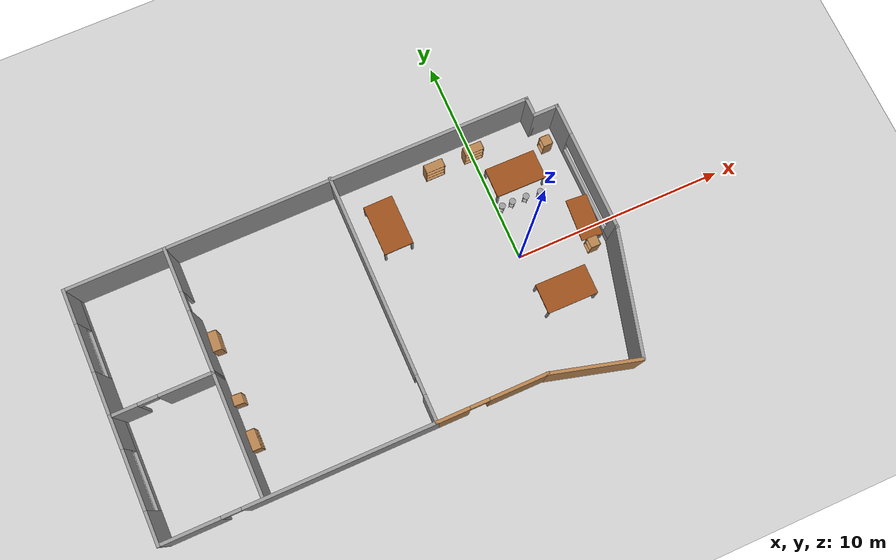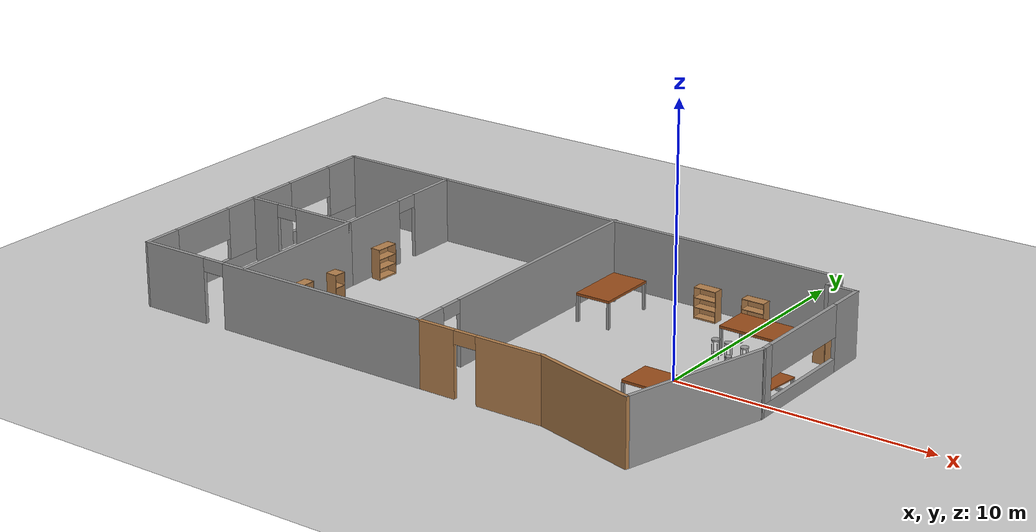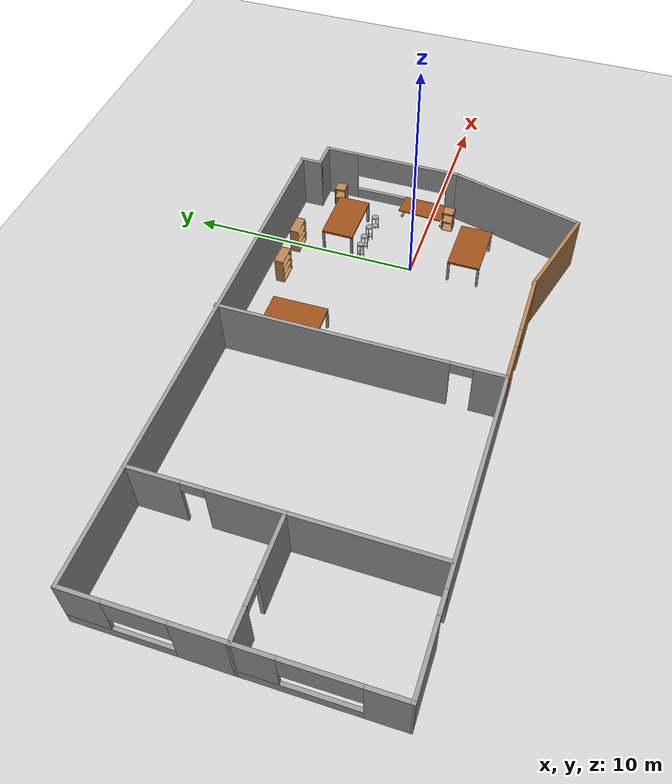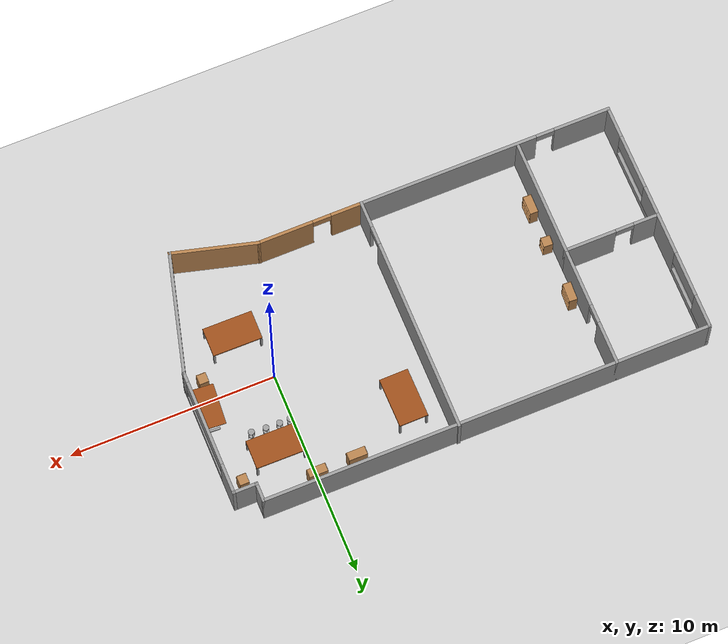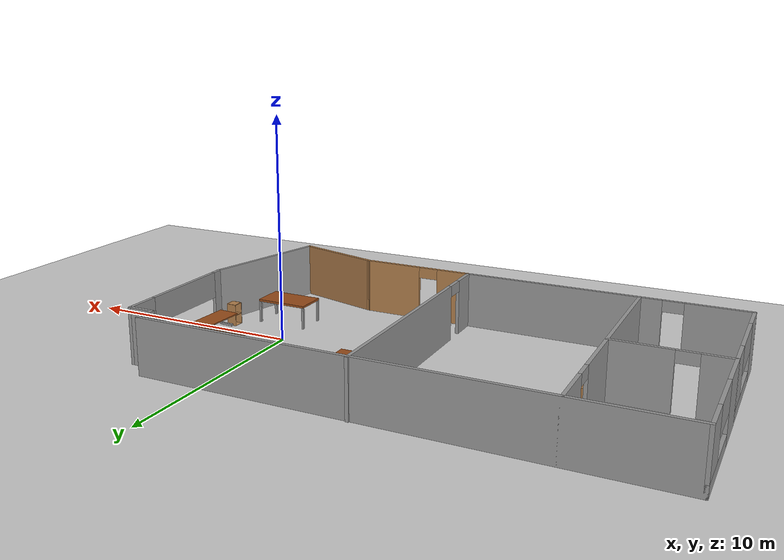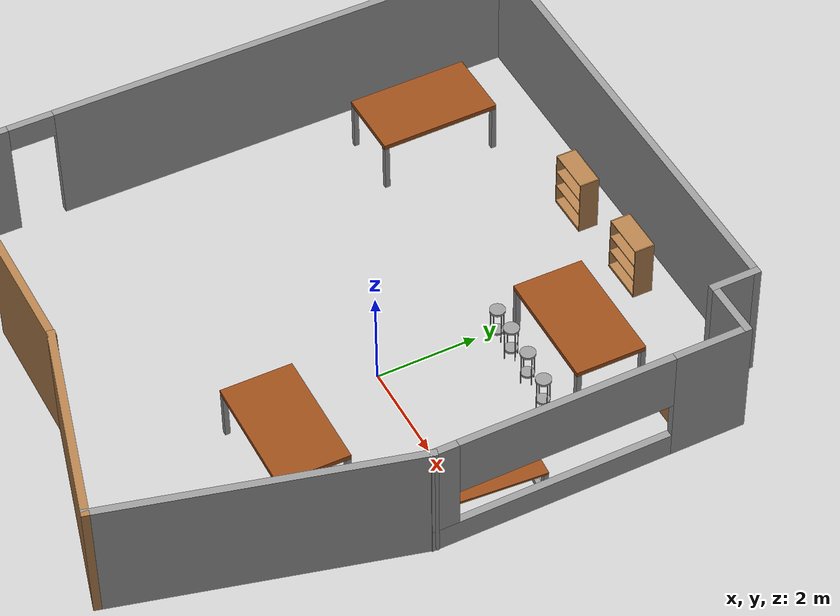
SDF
<sdf version="1.6">
 <world name="default">
  <light name="sun" type="directional">
   <pose>0 0 10 0 -0 0</pose>
   <diffuse>0.8 0.8 0.8 1</diffuse>
   <specular>0.2 0.2 0.2 1</specular>
   <attenuation>
    <range>1000</range>
    <constant>0.9</constant>
    <linear>0.01</linear>
    <quadratic>0.001</quadratic>
   </attenuation>
   <direction>-0.5 0.1 -0.9</direction>
  </light>
  <model name="ground_plane">
   <static>1</static>
   <link name="link">
    <collision name="collision">
     <geometry><plane><normal>0 0 1</normal><size>100 100</size></plane></geometry>
     <surface><friction><ode><mu>100</mu><mu2>50</mu2></ode></friction></surface>
    </collision>
    <visual name="visual">
     <cast_shadows>0</cast_shadows>
     <geometry><plane><normal>0 0 1</normal><size>100 100</size></plane></geometry>
     <material>
      <script><uri>file://media/materials/scripts/gazebo.material</uri><name>Gazebo/Grey</name></script>
     </material>
    </visual>
   </link>
  </model>
  <gravity>0 0 -9.8</gravity>
  <magnetic_field>6e-06 2.3e-05 -4.2e-05</magnetic_field>
  <atmosphere type="adiabatic"/>
  <physics name="default_physics" default="0" type="ode">
   <max_step_size>0.001</max_step_size>
   <real_time_factor>1</real_time_factor>
   <real_time_update_rate>1000</real_time_update_rate>
  </physics>
  <scene><ambient>0.4 0.4 0.4 1</ambient><background>0.7 0.7 0.7 1</background><shadows>1</shadows></scene>
  <spherical_coordinates>
   <surface_model>EARTH_WGS84</surface_model>
   <latitude_deg>0</latitude_deg>
   <longitude_deg>0</longitude_deg>
   <elevation>0</elevation>
   <heading_deg>0</heading_deg>
  </spherical_coordinates>
  <model name="cabinet">
   <static>1</static>
   <link name="cabinet_bottom_plate">
    <inertial>
     <pose>0 0 -1 0 -0 0</pose>
     <inertia><ixx>2.05</ixx><ixy>0</ixy><ixz>0</ixz><iyy>2.05</iyy><iyz>0</iyz><izz>2.05</izz></inertia>
     <mass>25</mass>
    </inertial>
    <collision name="cabinet_bottom_plate_geom">
     <pose>0 0 0.01 0 -0 0</pose>
     <geometry><box><size>0.45 0.45 0.02</size></box></geometry>
    </collision>
    <visual name="cabinet_bottom_plate_geom_visual">
     <pose>0 0 0.01 0 -0 0</pose>
     <geometry><box><size>0.45 0.45 0.02</size></box></geometry>
     <material>
      <script><uri>file://media/materials/scripts/gazebo.material</uri><name>Gazebo/Wood</name></script>
     </material>
    </visual>
    <collision name="cabinet_bottom_plate_geom_cabinet_back_plate">
     <pose>0.235 0 0.51 0 -0 0</pose>
     <geometry><box><size>0.02 0.45 1.02</size></box></geometry>
    </collision>
    <visual name="cabinet_bottom_plate_geom_cabinet_back_plate_visual">
     <pose>0.235 0 0.51 0 -0 0</pose>
     <geometry><box><size>0.02 0.45 1.02</size></box></geometry>
     <material>
      <script><uri>file://media/materials/scripts/gazebo.material</uri><name>Gazebo/Wood</name></script>
     </material>
    </visual>
    <collision name="cabinet_bottom_plate_geom_cabinet_left_plate">
     <pose>0 0.235 0.51 0 -0 0</pose>
     <geometry><box><size>0.45 0.02 1.02</size></box></geometry>
    </collision>
    <visual name="cabinet_bottom_plate_geom_cabinet_left_plate_visual">
     <pose>0 0.235 0.51 0 -0 0</pose>
     <geometry><box><size>0.45 0.02 1.02</size></box></geometry>
     <material>
      <script><uri>file://media/materials/scripts/gazebo.material</uri><name>Gazebo/Wood</name></script>
     </material>
    </visual>
    <collision name="cabinet_bottom_plate_geom_cabinet_middle_plate">
     <pose>0 0 0.51 0 -0 0</pose>
     <geometry><box><size>0.45 0.45 0.02</size></box></geometry>
    </collision>
    <visual name="cabinet_bottom_plate_geom_cabinet_middle_plate_visual">
     <pose>0 0 0.51 0 -0 0</pose>
     <geometry><box><size>0.45 0.45 0.02</size></box></geometry>
     <material>
      <script><uri>file://media/materials/scripts/gazebo.material</uri><name>Gazebo/Wood</name></script>
     </material>
    </visual>
    <collision name="cabinet_bottom_plate_geom_cabinet_right_plate">
     <pose>0 -0.235 0.51 0 -0 0</pose>
     <geometry><box><size>0.45 0.02 1.02</size></box></geometry>
    </collision>
    <visual name="cabinet_bottom_plate_geom_cabinet_right_plate_visual">
     <pose>0 -0.235 0.51 0 -0 0</pose>
     <geometry><box><size>0.45 0.02 1.02</size></box></geometry>
     <material>
      <script><uri>file://media/materials/scripts/gazebo.material</uri><name>Gazebo/Wood</name></script>
     </material>
    </visual>
    <collision name="cabinet_bottom_plate_geom_cabinet_top_plate">
     <pose>0 0 1.01 0 -0 0</pose>
     <geometry><box><size>0.45 0.45 0.02</size></box></geometry>
    </collision>
    <visual name="cabinet_bottom_plate_geom_cabinet_top_plate_visual">
     <pose>0 0 1.01 0 -0 0</pose>
     <geometry><box><size>0.45 0.45 0.02</size></box></geometry>
     <material>
      <script><uri>file://media/materials/scripts/gazebo.material</uri><name>Gazebo/Wood</name></script>
     </material>
    </visual>
   </link>
   <pose>3.24554 4.32799 0 0 -0 0</pose>
  </model>
  <model name="bookshelf">
   <static>1</static>
   <link name="link">
    <inertial><mass>1</mass></inertial>
    <collision name="back">
     <pose>0 0.005 0.6 0 -0 0</pose>
     <geometry><box><size>0.9 0.01 1.2</size></box></geometry>
    </collision>
    <visual name="visual1">
     <pose>0 0.005 0.6 0 -0 0</pose>
     <geometry><box><size>0.9 0.01 1.2</size></box></geometry>
     <material>
      <script><uri>file://media/materials/scripts/gazebo.material</uri><name>Gazebo/Wood</name></script>
     </material>
    </visual>
    <collision name="left_side">
     <pose>0.45 -0.195 0.6 0 -0 0</pose>
     <geometry><box><size>0.02 0.4 1.2</size></box></geometry>
    </collision>
    <visual name="visual2">
     <pose>0.45 -0.195 0.6 0 -0 0</pose>
     <geometry><box><size>0.02 0.4 1.2</size></box></geometry>
     <material>
      <script><uri>file://media/materials/scripts/gazebo.material</uri><name>Gazebo/Wood</name></script>
     </material>
    </visual>
    <collision name="right_side">
     <pose>-0.45 -0.195 0.6 0 -0 0</pose>
     <geometry><box><size>0.02 0.4 1.2</size></box></geometry>
    </collision>
    <visual name="visual3">
     <pose>-0.45 -0.195 0.6 0 -0 0</pose>
     <geometry><box><size>0.02 0.4 1.2</size></box></geometry>
     <material>
      <script><uri>file://media/materials/scripts/gazebo.material</uri><name>Gazebo/Wood</name></script>
     </material>
    </visual>
    <collision name="bottom">
     <pose>0 -0.195 0.03 0 -0 0</pose>
     <geometry><box><size>0.88 0.4 0.06</size></box></geometry>
    </collision>
    <visual name="visual4">
     <pose>0 -0.195 0.03 0 -0 0</pose>
     <geometry><box><size>0.88 0.4 0.06</size></box></geometry>
     <material>
      <script><uri>file://media/materials/scripts/gazebo.material</uri><name>Gazebo/Wood</name></script>
     </material>
    </visual>
    <collision name="top">
     <pose>0 -0.195 1.19 0 -0 0</pose>
     <geometry><box><size>0.88 0.4 0.02</size></box></geometry>
    </collision>
    <visual name="visual5">
     <pose>0 -0.195 1.19 0 -0 0</pose>
     <geometry><box><size>0.88 0.4 0.02</size></box></geometry>
     <material>
      <script><uri>file://media/materials/scripts/gazebo.material</uri><name>Gazebo/Wood</name></script>
     </material>
    </visual>
    <collision name="low_shelf">
     <pose>0 -0.195 0.43 0 -0 0</pose>
     <geometry><box><size>0.88 0.4 0.02</size></box></geometry>
    </collision>
    <visual name="visual6">
     <pose>0 -0.195 0.43 0 -0 0</pose>
     <geometry><box><size>0.88 0.4 0.02</size></box></geometry>
     <material>
      <script><uri>file://media/materials/scripts/gazebo.material</uri><name>Gazebo/Wood</name></script>
     </material>
    </visual>
    <collision name="high_shelf">
     <pose>0 -0.195 0.8 0 -0 0</pose>
     <geometry><box><size>0.88 0.4 0.02</size></box></geometry>
    </collision>
    <visual name="visual7">
     <pose>0 -0.195 0.8 0 -0 0</pose>
     <geometry><box><size>0.88 0.4 0.02</size></box></geometry>
     <material>
      <script><uri>file://media/materials/scripts/gazebo.material</uri><name>Gazebo/Wood</name></script>
     </material>
    </visual>
   </link>
   <pose>-0.009691 5.45445 0 0 -0 0</pose>
  </model>
  <model name="TaableInstructor">
   <link name="link_0">
    <pose>0 -0.22 0.364 0 -0 0</pose>
    <inertial>
     <mass>10</mass>
     <inertia>
      <ixx>0.166667</ixx>
      <ixy>0</ixy>
      <ixz>0</ixz>
      <iyy>0.166667</iyy>
      <iyz>0</iyz>
      <izz>0.166667</izz>
     </inertia>
    </inertial>
    <visual name="visual">
     <geometry><box><size>2 1 0.05</size></box></geometry>
     <material>
      <lighting>1</lighting>
      <script><uri>file://media/materials/scripts/gazebo.material</uri><name>Gazebo/Grey</name></script>
      <shader type="pixel"><normal_map>__default__</normal_map></shader>
      <ambient>0.6 0.3 0.1 1</ambient>
      <diffuse>0.7 0.7 0.7 1</diffuse>
      <specular>0.01 0.01 0.01 1</specular>
      <emissive>0 0 0 1</emissive>
     </material>
    </visual>
    <collision name="collision">
     <geometry><box><size>2 1 0.05</size></box></geometry>
     <surface>
      <friction>
       <ode><mu>1</mu><mu2>1</mu2><fdir1>0 0 0</fdir1><slip1>0</slip1><slip2>0</slip2></ode>
       <torsional>
        <coefficient>1</coefficient>
        <patch_radius>0</patch_radius>
        <surface_radius>0</surface_radius>
        <use_patch_radius>1</use_patch_radius>
        <ode><slip>0</slip></ode>
       </torsional>
      </friction>
      <bounce><restitution_coefficient>0</restitution_coefficient><threshold>1e+06</threshold></bounce>
      <contact>
       <collide_without_contact>0</collide_without_contact>
       <collide_without_contact_bitmask>1</collide_without_contact_bitmask>
       <collide_bitmask>1</collide_bitmask>
       <ode>
        <soft_cfm>0</soft_cfm>
        <soft_erp>0.2</soft_erp>
        <kp>1e+13</kp>
        <kd>1</kd>
        <max_vel>0.01</max_vel>
        <min_depth>0</min_depth>
       </ode>
       <bullet>
        <split_impulse>1</split_impulse>
        <split_impulse_penetration_threshold>-0.01</split_impulse_penetration_threshold>
        <soft_cfm>0</soft_cfm>
        <soft_erp>0.2</soft_erp>
        <kp>1e+13</kp>
        <kd>1</kd>
       </bullet>
      </contact>
     </surface>
    </collision>
   </link>
   <link name="link_1">
    <pose>-0.95 0.23 0.039 0 -0 0</pose>
    <inertial>
     <mass>1</mass>
     <inertia>
      <ixx>0.166667</ixx>
      <ixy>0</ixy>
      <ixz>0</ixz>
      <iyy>0.166667</iyy>
      <iyz>0</iyz>
      <izz>0.166667</izz>
     </inertia>
    </inertial>
    <visual name="visual">
     <geometry><box><size>0.1 0.1 0.6</size></box></geometry>
     <material>
      <lighting>1</lighting>
      <script><uri>file://media/materials/scripts/gazebo.material</uri><name>Gazebo/Grey</name></script>
      <shader type="pixel"><normal_map>__default__</normal_map></shader>
      <ambient>0.3 0.3 0.3 1</ambient>
      <diffuse>0.7 0.7 0.7 1</diffuse>
      <specular>0.01 0.01 0.01 1</specular>
      <emissive>0 0 0 1</emissive>
     </material>
    </visual>
    <collision name="collision">
     <geometry><box><size>0.1 0.1 0.6</size></box></geometry>
     <surface>
      <friction>
       <ode><mu>1</mu><mu2>1</mu2><fdir1>0 0 0</fdir1><slip1>0</slip1><slip2>0</slip2></ode>
       <torsional>
        <coefficient>1</coefficient>
        <patch_radius>0</patch_radius>
        <surface_radius>0</surface_radius>
        <use_patch_radius>1</use_patch_radius>
        <ode><slip>0</slip></ode>
       </torsional>
      </friction>
      <bounce><restitution_coefficient>0</restitution_coefficient><threshold>1e+06</threshold></bounce>
      <contact>
       <collide_without_contact>0</collide_without_contact>
       <collide_without_contact_bitmask>1</collide_without_contact_bitmask>
       <collide_bitmask>1</collide_bitmask>
       <ode>
        <soft_cfm>0</soft_cfm>
        <soft_erp>0.2</soft_erp>
        <kp>1e+13</kp>
        <kd>1</kd>
        <max_vel>0.01</max_vel>
        <min_depth>0</min_depth>
       </ode>
       <bullet>
        <split_impulse>1</split_impulse>
        <split_impulse_penetration_threshold>-0.01</split_impulse_penetration_threshold>
        <soft_cfm>0</soft_cfm>
        <soft_erp>0.2</soft_erp>
        <kp>1e+13</kp>
        <kd>1</kd>
       </bullet>
      </contact>
     </surface>
    </collision>
   </link>
   <link name="link_1_clone">
    <pose>0.95 0.23 0.039 0 -0 0</pose>
    <inertial>
     <mass>1</mass>
     <inertia>
      <ixx>0.166667</ixx>
      <ixy>0</ixy>
      <ixz>0</ixz>
      <iyy>0.166667</iyy>
      <iyz>0</iyz>
      <izz>0.166667</izz>
     </inertia>
    </inertial>
    <visual name="visual">
     <geometry><box><size>0.1 0.1 0.6</size></box></geometry>
     <material>
      <lighting>1</lighting>
      <script><uri>file://media/materials/scripts/gazebo.material</uri><name>Gazebo/Grey</name></script>
      <shader type="pixel"><normal_map>__default__</normal_map></shader>
      <ambient>0.3 0.3 0.3 1</ambient>
      <diffuse>0.7 0.7 0.7 1</diffuse>
      <specular>0.01 0.01 0.01 1</specular>
      <emissive>0 0 0 1</emissive>
     </material>
    </visual>
    <collision name="collision">
     <geometry><box><size>0.1 0.1 0.6</size></box></geometry>
     <surface>
      <friction>
       <ode><mu>1</mu><mu2>1</mu2><fdir1>0 0 0</fdir1><slip1>0</slip1><slip2>0</slip2></ode>
       <torsional>
        <coefficient>1</coefficient>
        <patch_radius>0</patch_radius>
        <surface_radius>0</surface_radius>
        <use_patch_radius>1</use_patch_radius>
        <ode><slip>0</slip></ode>
       </torsional>
      </friction>
      <bounce><restitution_coefficient>0</restitution_coefficient><threshold>1e+06</threshold></bounce>
      <contact>
       <collide_without_contact>0</collide_without_contact>
       <collide_without_contact_bitmask>1</collide_without_contact_bitmask>
       <collide_bitmask>1</collide_bitmask>
       <ode>
        <soft_cfm>0</soft_cfm>
        <soft_erp>0.2</soft_erp>
        <kp>1e+13</kp>
        <kd>1</kd>
        <max_vel>0.01</max_vel>
        <min_depth>0</min_depth>
       </ode>
       <bullet>
        <split_impulse>1</split_impulse>
        <split_impulse_penetration_threshold>-0.01</split_impulse_penetration_threshold>
        <soft_cfm>0</soft_cfm>
        <soft_erp>0.2</soft_erp>
        <kp>1e+13</kp>
        <kd>1</kd>
       </bullet>
      </contact>
     </surface>
    </collision>
   </link>
   <link name="link_1_clone_0">
    <pose>-0.95 -0.12 -0.211 1.57 -0 0</pose>
    <inertial>
     <mass>1</mass>
     <inertia>
      <ixx>0.166667</ixx>
      <ixy>0</ixy>
      <ixz>0</ixz>
      <iyy>0.166667</iyy>
      <iyz>0</iyz>
      <izz>0.166667</izz>
     </inertia>
    </inertial>
    <visual name="visual">
     <geometry><box><size>0.1 0.1 0.6</size></box></geometry>
     <material>
      <lighting>1</lighting>
      <script><uri>file://media/materials/scripts/gazebo.material</uri><name>Gazebo/Grey</name></script>
      <shader type="pixel"><normal_map>__default__</normal_map></shader>
      <ambient>0.3 0.3 0.3 1</ambient>
      <diffuse>0.7 0.7 0.7 1</diffuse>
      <specular>0.01 0.01 0.01 1</specular>
      <emissive>0 0 0 1</emissive>
     </material>
    </visual>
    <collision name="collision">
     <geometry><box><size>0.1 0.1 0.6</size></box></geometry>
     <surface>
      <friction>
       <ode><mu>1</mu><mu2>1</mu2><fdir1>0 0 0</fdir1><slip1>0</slip1><slip2>0</slip2></ode>
       <torsional>
        <coefficient>1</coefficient>
        <patch_radius>0</patch_radius>
        <surface_radius>0</surface_radius>
        <use_patch_radius>1</use_patch_radius>
        <ode><slip>0</slip></ode>
       </torsional>
      </friction>
      <bounce><restitution_coefficient>0</restitution_coefficient><threshold>1e+06</threshold></bounce>
      <contact>
       <collide_without_contact>0</collide_without_contact>
       <collide_without_contact_bitmask>1</collide_without_contact_bitmask>
       <collide_bitmask>1</collide_bitmask>
       <ode>
        <soft_cfm>0</soft_cfm>
        <soft_erp>0.2</soft_erp>
        <kp>1e+13</kp>
        <kd>1</kd>
        <max_vel>0.01</max_vel>
        <min_depth>0</min_depth>
       </ode>
       <bullet>
        <split_impulse>1</split_impulse>
        <split_impulse_penetration_threshold>-0.01</split_impulse_penetration_threshold>
        <soft_cfm>0</soft_cfm>
        <soft_erp>0.2</soft_erp>
        <kp>1e+13</kp>
        <kd>1</kd>
       </bullet>
      </contact>
     </surface>
    </collision>
   </link>
   <link name="link_1_clone_0_clone">
    <pose>0.95 -0.12 -0.231 1.57 -0 0</pose>
    <inertial>
     <mass>1</mass>
     <inertia>
      <ixx>0.166667</ixx>
      <ixy>0</ixy>
      <ixz>0</ixz>
      <iyy>0.166667</iyy>
      <iyz>0</iyz>
      <izz>0.166667</izz>
     </inertia>
    </inertial>
    <visual name="visual">
     <geometry><box><size>0.1 0.1 0.6</size></box></geometry>
     <material>
      <lighting>1</lighting>
      <script><uri>file://media/materials/scripts/gazebo.material</uri><name>Gazebo/Grey</name></script>
      <shader type="pixel"><normal_map>__default__</normal_map></shader>
      <ambient>0.3 0.3 0.3 1</ambient>
      <diffuse>0.7 0.7 0.7 1</diffuse>
      <specular>0.01 0.01 0.01 1</specular>
      <emissive>0 0 0 1</emissive>
     </material>
    </visual>
    <collision name="collision">
     <geometry><box><size>0.1 0.1 0.6</size></box></geometry>
     <surface>
      <friction>
       <ode><mu>1</mu><mu2>1</mu2><fdir1>0 0 0</fdir1><slip1>0</slip1><slip2>0</slip2></ode>
       <torsional>
        <coefficient>1</coefficient>
        <patch_radius>0</patch_radius>
        <surface_radius>0</surface_radius>
        <use_patch_radius>1</use_patch_radius>
        <ode><slip>0</slip></ode>
       </torsional>
      </friction>
      <bounce><restitution_coefficient>0</restitution_coefficient><threshold>1e+06</threshold></bounce>
      <contact>
       <collide_without_contact>0</collide_without_contact>
       <collide_without_contact_bitmask>1</collide_without_contact_bitmask>
       <collide_bitmask>1</collide_bitmask>
       <ode>
        <soft_cfm>0</soft_cfm>
        <soft_erp>0.2</soft_erp>
        <kp>1e+13</kp>
        <kd>1</kd>
        <max_vel>0.01</max_vel>
        <min_depth>0</min_depth>
       </ode>
       <bullet>
        <split_impulse>1</split_impulse>
        <split_impulse_penetration_threshold>-0.01</split_impulse_penetration_threshold>
        <soft_cfm>0</soft_cfm>
        <soft_erp>0.2</soft_erp>
        <kp>1e+13</kp>
        <kd>1</kd>
       </bullet>
      </contact>
     </surface>
    </collision>
   </link>
   <joint name="link_0_JOINT_0" type="fixed">
    <parent>link_0</parent>
    <child>link_1_clone</child>
    <physics>
     <ode><limit><cfm>0</cfm><erp>0.2</erp></limit><suspension><cfm>0</cfm><erp>0.2</erp></suspension></ode>
    </physics>
   </joint>
   <joint name="link_0_JOINT_1" type="fixed">
    <parent>link_0</parent>
    <child>link_1</child>
    <physics>
     <ode><limit><cfm>0</cfm><erp>0.2</erp></limit><suspension><cfm>0</cfm><erp>0.2</erp></suspension></ode>
    </physics>
   </joint>
   <joint name="link_1_JOINT_2" type="fixed">
    <parent>link_1</parent>
    <child>link_1_clone_0</child>
    <physics>
     <ode><limit><cfm>0</cfm><erp>0.2</erp></limit><suspension><cfm>0</cfm><erp>0.2</erp></suspension></ode>
    </physics>
   </joint>
   <joint name="link_1_clone_JOINT_4" type="fixed">
    <parent>link_1_clone</parent>
    <child>link_1_clone_0_clone</child>
    <physics>
     <ode><limit><cfm>0</cfm><erp>0.2</erp></limit><suspension><cfm>0</cfm><erp>0.2</erp></suspension></ode>
    </physics>
   </joint>
   <static>0</static>
   <pose>3.56448 0.389819 0.271601 0.0008 -0.010533 -1.64038</pose>
  </model>
  <model name="TableStudent">
   <link name="link_6">
    <pose>0 0 0.44 0 -0 0</pose>
    <inertial>
     <mass>1</mass>
     <inertia>
      <ixx>0.166667</ixx>
      <ixy>0</ixy>
      <ixz>0</ixz>
      <iyy>0.166667</iyy>
      <iyz>0</iyz>
      <izz>0.166667</izz>
     </inertia>
    </inertial>
    <visual name="visual">
     <geometry><box><size>2.4 1.4 0.1</size></box></geometry>
     <material>
      <lighting>1</lighting>
      <script><uri>file://media/materials/scripts/gazebo.material</uri><name>Gazebo/Grey</name></script>
      <shader type="pixel"><normal_map>__default__</normal_map></shader>
      <ambient>0.6 0.3 0.1 1</ambient>
      <diffuse>0.7 0.7 0.7 1</diffuse>
      <specular>0.01 0.01 0.01 1</specular>
      <emissive>0 0 0 1</emissive>
     </material>
    </visual>
    <collision name="collision">
     <geometry><box><size>2.4 1.4 0.1</size></box></geometry>
     <surface>
      <friction>
       <ode><mu>1</mu><mu2>1</mu2><fdir1>0 0 0</fdir1><slip1>0</slip1><slip2>0</slip2></ode>
       <torsional>
        <coefficient>1</coefficient>
        <patch_radius>0</patch_radius>
        <surface_radius>0</surface_radius>
        <use_patch_radius>1</use_patch_radius>
        <ode><slip>0</slip></ode>
       </torsional>
      </friction>
      <bounce><restitution_coefficient>0</restitution_coefficient><threshold>1e+06</threshold></bounce>
      <contact>
       <collide_without_contact>0</collide_without_contact>
       <collide_without_contact_bitmask>1</collide_without_contact_bitmask>
       <collide_bitmask>1</collide_bitmask>
       <ode>
        <soft_cfm>0</soft_cfm>
        <soft_erp>0.2</soft_erp>
        <kp>1e+13</kp>
        <kd>1</kd>
        <max_vel>0.01</max_vel>
        <min_depth>0</min_depth>
       </ode>
       <bullet>
        <split_impulse>1</split_impulse>
        <split_impulse_penetration_threshold>-0.01</split_impulse_penetration_threshold>
        <soft_cfm>0</soft_cfm>
        <soft_erp>0.2</soft_erp>
        <kp>1e+13</kp>
        <kd>1</kd>
       </bullet>
      </contact>
     </surface>
    </collision>
   </link>
   <link name="link_7">
    <pose>1.15 0.65 -0.11 0 -0 0</pose>
    <inertial>
     <mass>2</mass>
     <inertia>
      <ixx>0.166667</ixx>
      <ixy>0</ixy>
      <ixz>0</ixz>
      <iyy>0.166667</iyy>
      <iyz>0</iyz>
      <izz>0.166667</izz>
     </inertia>
    </inertial>
    <visual name="visual">
     <geometry><box><size>0.1 0.1 1</size></box></geometry>
     <material>
      <lighting>1</lighting>
      <script><uri>file://media/materials/scripts/gazebo.material</uri><name>Gazebo/Grey</name></script>
      <shader type="pixel"><normal_map>__default__</normal_map></shader>
      <ambient>0.3 0.3 0.3 1</ambient>
      <diffuse>0.7 0.7 0.7 1</diffuse>
      <specular>0.01 0.01 0.01 1</specular>
      <emissive>0 0 0 1</emissive>
     </material>
    </visual>
    <collision name="collision">
     <geometry><box><size>0.1 0.1 1</size></box></geometry>
     <surface>
      <friction>
       <ode><mu>1</mu><mu2>1</mu2><fdir1>0 0 0</fdir1><slip1>0</slip1><slip2>0</slip2></ode>
       <torsional>
        <coefficient>1</coefficient>
        <patch_radius>0</patch_radius>
        <surface_radius>0</surface_radius>
        <use_patch_radius>1</use_patch_radius>
        <ode><slip>0</slip></ode>
       </torsional>
      </friction>
      <bounce><restitution_coefficient>0</restitution_coefficient><threshold>1e+06</threshold></bounce>
      <contact>
       <collide_without_contact>0</collide_without_contact>
       <collide_without_contact_bitmask>1</collide_without_contact_bitmask>
       <collide_bitmask>1</collide_bitmask>
       <ode>
        <soft_cfm>0</soft_cfm>
        <soft_erp>0.2</soft_erp>
        <kp>1e+13</kp>
        <kd>1</kd>
        <max_vel>0.01</max_vel>
        <min_depth>0</min_depth>
       </ode>
       <bullet>
        <split_impulse>1</split_impulse>
        <split_impulse_penetration_threshold>-0.01</split_impulse_penetration_threshold>
        <soft_cfm>0</soft_cfm>
        <soft_erp>0.2</soft_erp>
        <kp>1e+13</kp>
        <kd>1</kd>
       </bullet>
      </contact>
     </surface>
    </collision>
   </link>
   <link name="link_7_clone">
    <pose>-1.15 -0.65 -0.11 0 -0 0</pose>
    <inertial>
     <mass>2</mass>
     <inertia>
      <ixx>0.166667</ixx>
      <ixy>0</ixy>
      <ixz>0</ixz>
      <iyy>0.166667</iyy>
      <iyz>0</iyz>
      <izz>0.166667</izz>
     </inertia>
    </inertial>
    <visual name="visual">
     <geometry><box><size>0.1 0.1 1</size></box></geometry>
     <material>
      <lighting>1</lighting>
      <script><uri>file://media/materials/scripts/gazebo.material</uri><name>Gazebo/Grey</name></script>
      <shader type="pixel"><normal_map>__default__</normal_map></shader>
      <ambient>0.3 0.3 0.3 1</ambient>
      <diffuse>0.7 0.7 0.7 1</diffuse>
      <specular>0.01 0.01 0.01 1</specular>
      <emissive>0 0 0 1</emissive>
     </material>
    </visual>
    <collision name="collision">
     <geometry><box><size>0.1 0.1 1</size></box></geometry>
     <surface>
      <friction>
       <ode><mu>1</mu><mu2>1</mu2><fdir1>0 0 0</fdir1><slip1>0</slip1><slip2>0</slip2></ode>
       <torsional>
        <coefficient>1</coefficient>
        <patch_radius>0</patch_radius>
        <surface_radius>0</surface_radius>
        <use_patch_radius>1</use_patch_radius>
        <ode><slip>0</slip></ode>
       </torsional>
      </friction>
      <bounce><restitution_coefficient>0</restitution_coefficient><threshold>1e+06</threshold></bounce>
      <contact>
       <collide_without_contact>0</collide_without_contact>
       <collide_without_contact_bitmask>1</collide_without_contact_bitmask>
       <collide_bitmask>1</collide_bitmask>
       <ode>
        <soft_cfm>0</soft_cfm>
        <soft_erp>0.2</soft_erp>
        <kp>1e+13</kp>
        <kd>1</kd>
        <max_vel>0.01</max_vel>
        <min_depth>0</min_depth>
       </ode>
       <bullet>
        <split_impulse>1</split_impulse>
        <split_impulse_penetration_threshold>-0.01</split_impulse_penetration_threshold>
        <soft_cfm>0</soft_cfm>
        <soft_erp>0.2</soft_erp>
        <kp>1e+13</kp>
        <kd>1</kd>
       </bullet>
      </contact>
     </surface>
    </collision>
   </link>
   <link name="link_7_clone_0">
    <pose>1.15 -0.65 -0.11 0 -0 0</pose>
    <inertial>
     <mass>2</mass>
     <inertia>
      <ixx>0.166667</ixx>
      <ixy>0</ixy>
      <ixz>0</ixz>
      <iyy>0.166667</iyy>
      <iyz>0</iyz>
      <izz>0.166667</izz>
     </inertia>
    </inertial>
    <visual name="visual">
     <geometry><box><size>0.1 0.1 1</size></box></geometry>
     <material>
      <lighting>1</lighting>
      <script><uri>file://media/materials/scripts/gazebo.material</uri><name>Gazebo/Grey</name></script>
      <shader type="pixel"><normal_map>__default__</normal_map></shader>
      <ambient>0.3 0.3 0.3 1</ambient>
      <diffuse>0.7 0.7 0.7 1</diffuse>
      <specular>0.01 0.01 0.01 1</specular>
      <emissive>0 0 0 1</emissive>
     </material>
    </visual>
    <collision name="collision">
     <geometry><box><size>0.1 0.1 1</size></box></geometry>
     <surface>
      <friction>
       <ode><mu>1</mu><mu2>1</mu2><fdir1>0 0 0</fdir1><slip1>0</slip1><slip2>0</slip2></ode>
       <torsional>
        <coefficient>1</coefficient>
        <patch_radius>0</patch_radius>
        <surface_radius>0</surface_radius>
        <use_patch_radius>1</use_patch_radius>
        <ode><slip>0</slip></ode>
       </torsional>
      </friction>
      <bounce><restitution_coefficient>0</restitution_coefficient><threshold>1e+06</threshold></bounce>
      <contact>
       <collide_without_contact>0</collide_without_contact>
       <collide_without_contact_bitmask>1</collide_without_contact_bitmask>
       <collide_bitmask>1</collide_bitmask>
       <ode>
        <soft_cfm>0</soft_cfm>
        <soft_erp>0.2</soft_erp>
        <kp>1e+13</kp>
        <kd>1</kd>
        <max_vel>0.01</max_vel>
        <min_depth>0</min_depth>
       </ode>
       <bullet>
        <split_impulse>1</split_impulse>
        <split_impulse_penetration_threshold>-0.01</split_impulse_penetration_threshold>
        <soft_cfm>0</soft_cfm>
        <soft_erp>0.2</soft_erp>
        <kp>1e+13</kp>
        <kd>1</kd>
       </bullet>
      </contact>
     </surface>
    </collision>
   </link>
   <link name="link_7_clone_1">
    <pose>-1.15 0.65 -0.11 0 -0 0</pose>
    <inertial>
     <mass>2</mass>
     <inertia>
      <ixx>0.166667</ixx>
      <ixy>0</ixy>
      <ixz>0</ixz>
      <iyy>0.166667</iyy>
      <iyz>0</iyz>
      <izz>0.166667</izz>
     </inertia>
    </inertial>
    <visual name="visual">
     <geometry><box><size>0.1 0.1 1</size></box></geometry>
     <material>
      <lighting>1</lighting>
      <script><uri>file://media/materials/scripts/gazebo.material</uri><name>Gazebo/Grey</name></script>
      <shader type="pixel"><normal_map>__default__</normal_map></shader>
      <ambient>0.3 0.3 0.3 1</ambient>
      <diffuse>0.7 0.7 0.7 1</diffuse>
      <specular>0.01 0.01 0.01 1</specular>
      <emissive>0 0 0 1</emissive>
     </material>
    </visual>
    <collision name="collision">
     <geometry><box><size>0.1 0.1 1</size></box></geometry>
     <surface>
      <friction>
       <ode><mu>1</mu><mu2>1</mu2><fdir1>0 0 0</fdir1><slip1>0</slip1><slip2>0</slip2></ode>
       <torsional>
        <coefficient>1</coefficient>
        <patch_radius>0</patch_radius>
        <surface_radius>0</surface_radius>
        <use_patch_radius>1</use_patch_radius>
        <ode><slip>0</slip></ode>
       </torsional>
      </friction>
      <bounce><restitution_coefficient>0</restitution_coefficient><threshold>1e+06</threshold></bounce>
      <contact>
       <collide_without_contact>0</collide_without_contact>
       <collide_without_contact_bitmask>1</collide_without_contact_bitmask>
       <collide_bitmask>1</collide_bitmask>
       <ode>
        <soft_cfm>0</soft_cfm>
        <soft_erp>0.2</soft_erp>
        <kp>1e+13</kp>
        <kd>1</kd>
        <max_vel>0.01</max_vel>
        <min_depth>0</min_depth>
       </ode>
       <bullet>
        <split_impulse>1</split_impulse>
        <split_impulse_penetration_threshold>-0.01</split_impulse_penetration_threshold>
        <soft_cfm>0</soft_cfm>
        <soft_erp>0.2</soft_erp>
        <kp>1e+13</kp>
        <kd>1</kd>
       </bullet>
      </contact>
     </surface>
    </collision>
   </link>
   <joint name="link_6_JOINT_10" type="fixed">
    <parent>link_6</parent>
    <child>link_7_clone</child>
    <physics>
     <ode><limit><cfm>0</cfm><erp>0.2</erp></limit><suspension><cfm>0</cfm><erp>0.2</erp></suspension></ode>
    </physics>
   </joint>
   <joint name="link_6_JOINT_11" type="fixed">
    <parent>link_6</parent>
    <child>link_7_clone_1</child>
    <physics>
     <ode><limit><cfm>0</cfm><erp>0.2</erp></limit><suspension><cfm>0</cfm><erp>0.2</erp></suspension></ode>
    </physics>
   </joint>
   <joint name="link_6_JOINT_12" type="fixed">
    <parent>link_6</parent>
    <child>link_7</child>
    <physics>
     <ode><limit><cfm>0</cfm><erp>0.2</erp></limit><suspension><cfm>0</cfm><erp>0.2</erp></suspension></ode>
    </physics>
   </joint>
   <joint name="link_6_JOINT_13" type="revolute">
    <parent>link_6</parent>
    <child>link_7_clone_0</child>
    <axis>
     <xyz>1 0 0</xyz>
     <use_parent_model_frame>0</use_parent_model_frame>
     <limit>
      <lower>-1.79769e+308</lower>
      <upper>1.79769e+308</upper>
      <effort>-1</effort>
      <velocity>-1</velocity>
     </limit>
     <dynamics>
      <spring_reference>0</spring_reference>
      <spring_stiffness>0</spring_stiffness>
      <damping>0</damping>
     </dynamics>
    </axis>
    <physics>
     <ode><limit><cfm>0</cfm><erp>0.2</erp></limit><suspension><cfm>0</cfm><erp>0.2</erp></suspension></ode>
    </physics>
   </joint>
   <static>0</static>
   <pose>1.2779 3.42779 0.61 0 0 -0.009212</pose>
  </model>
  <model name="TableStudent_0">
   <link name="link_6">
    <pose>0 0 0.44 0 -0 0</pose>
    <inertial>
     <mass>1</mass>
     <inertia>
      <ixx>0.166667</ixx>
      <ixy>0</ixy>
      <ixz>0</ixz>
      <iyy>0.166667</iyy>
      <iyz>0</iyz>
      <izz>0.166667</izz>
     </inertia>
    </inertial>
    <visual name="visual">
     <geometry><box><size>2.4 1.4 0.1</size></box></geometry>
     <material>
      <lighting>1</lighting>
      <script><uri>file://media/materials/scripts/gazebo.material</uri><name>Gazebo/Grey</name></script>
      <shader type="pixel"><normal_map>__default__</normal_map></shader>
      <ambient>0.6 0.3 0.1 1</ambient>
      <diffuse>0.7 0.7 0.7 1</diffuse>
      <specular>0.01 0.01 0.01 1</specular>
      <emissive>0 0 0 1</emissive>
     </material>
    </visual>
    <collision name="collision">
     <geometry><box><size>2.4 1.4 0.1</size></box></geometry>
     <surface>
      <friction>
       <ode><mu>1</mu><mu2>1</mu2><fdir1>0 0 0</fdir1><slip1>0</slip1><slip2>0</slip2></ode>
       <torsional>
        <coefficient>1</coefficient>
        <patch_radius>0</patch_radius>
        <surface_radius>0</surface_radius>
        <use_patch_radius>1</use_patch_radius>
        <ode><slip>0</slip></ode>
       </torsional>
      </friction>
      <bounce><restitution_coefficient>0</restitution_coefficient><threshold>1e+06</threshold></bounce>
      <contact>
       <collide_without_contact>0</collide_without_contact>
       <collide_without_contact_bitmask>1</collide_without_contact_bitmask>
       <collide_bitmask>1</collide_bitmask>
       <ode>
        <soft_cfm>0</soft_cfm>
        <soft_erp>0.2</soft_erp>
        <kp>1e+13</kp>
        <kd>1</kd>
        <max_vel>0.01</max_vel>
        <min_depth>0</min_depth>
       </ode>
       <bullet>
        <split_impulse>1</split_impulse>
        <split_impulse_penetration_threshold>-0.01</split_impulse_penetration_threshold>
        <soft_cfm>0</soft_cfm>
        <soft_erp>0.2</soft_erp>
        <kp>1e+13</kp>
        <kd>1</kd>
       </bullet>
      </contact>
     </surface>
    </collision>
   </link>
   <link name="link_7">
    <pose>1.15 0.65 -0.11 0 -0 0</pose>
    <inertial>
     <mass>2</mass>
     <inertia>
      <ixx>0.166667</ixx>
      <ixy>0</ixy>
      <ixz>0</ixz>
      <iyy>0.166667</iyy>
      <iyz>0</iyz>
      <izz>0.166667</izz>
     </inertia>
    </inertial>
    <visual name="visual">
     <geometry><box><size>0.1 0.1 1</size></box></geometry>
     <material>
      <lighting>1</lighting>
      <script><uri>file://media/materials/scripts/gazebo.material</uri><name>Gazebo/Grey</name></script>
      <shader type="pixel"><normal_map>__default__</normal_map></shader>
      <ambient>0.3 0.3 0.3 1</ambient>
      <diffuse>0.7 0.7 0.7 1</diffuse>
      <specular>0.01 0.01 0.01 1</specular>
      <emissive>0 0 0 1</emissive>
     </material>
    </visual>
    <collision name="collision">
     <geometry><box><size>0.1 0.1 1</size></box></geometry>
     <surface>
      <friction>
       <ode><mu>1</mu><mu2>1</mu2><fdir1>0 0 0</fdir1><slip1>0</slip1><slip2>0</slip2></ode>
       <torsional>
        <coefficient>1</coefficient>
        <patch_radius>0</patch_radius>
        <surface_radius>0</surface_radius>
        <use_patch_radius>1</use_patch_radius>
        <ode><slip>0</slip></ode>
       </torsional>
      </friction>
      <bounce><restitution_coefficient>0</restitution_coefficient><threshold>1e+06</threshold></bounce>
      <contact>
       <collide_without_contact>0</collide_without_contact>
       <collide_without_contact_bitmask>1</collide_without_contact_bitmask>
       <collide_bitmask>1</collide_bitmask>
       <ode>
        <soft_cfm>0</soft_cfm>
        <soft_erp>0.2</soft_erp>
        <kp>1e+13</kp>
        <kd>1</kd>
        <max_vel>0.01</max_vel>
        <min_depth>0</min_depth>
       </ode>
       <bullet>
        <split_impulse>1</split_impulse>
        <split_impulse_penetration_threshold>-0.01</split_impulse_penetration_threshold>
        <soft_cfm>0</soft_cfm>
        <soft_erp>0.2</soft_erp>
        <kp>1e+13</kp>
        <kd>1</kd>
       </bullet>
      </contact>
     </surface>
    </collision>
   </link>
   <link name="link_7_clone">
    <pose>-1.15 -0.65 -0.11 0 -0 0</pose>
    <inertial>
     <mass>2</mass>
     <inertia>
      <ixx>0.166667</ixx>
      <ixy>0</ixy>
      <ixz>0</ixz>
      <iyy>0.166667</iyy>
      <iyz>0</iyz>
      <izz>0.166667</izz>
     </inertia>
    </inertial>
    <visual name="visual">
     <geometry><box><size>0.1 0.1 1</size></box></geometry>
     <material>
      <lighting>1</lighting>
      <script><uri>file://media/materials/scripts/gazebo.material</uri><name>Gazebo/Grey</name></script>
      <shader type="pixel"><normal_map>__default__</normal_map></shader>
      <ambient>0.3 0.3 0.3 1</ambient>
      <diffuse>0.7 0.7 0.7 1</diffuse>
      <specular>0.01 0.01 0.01 1</specular>
      <emissive>0 0 0 1</emissive>
     </material>
    </visual>
    <collision name="collision">
     <geometry><box><size>0.1 0.1 1</size></box></geometry>
     <surface>
      <friction>
       <ode><mu>1</mu><mu2>1</mu2><fdir1>0 0 0</fdir1><slip1>0</slip1><slip2>0</slip2></ode>
       <torsional>
        <coefficient>1</coefficient>
        <patch_radius>0</patch_radius>
        <surface_radius>0</surface_radius>
        <use_patch_radius>1</use_patch_radius>
        <ode><slip>0</slip></ode>
       </torsional>
      </friction>
      <bounce><restitution_coefficient>0</restitution_coefficient><threshold>1e+06</threshold></bounce>
      <contact>
       <collide_without_contact>0</collide_without_contact>
       <collide_without_contact_bitmask>1</collide_without_contact_bitmask>
       <collide_bitmask>1</collide_bitmask>
       <ode>
        <soft_cfm>0</soft_cfm>
        <soft_erp>0.2</soft_erp>
        <kp>1e+13</kp>
        <kd>1</kd>
        <max_vel>0.01</max_vel>
        <min_depth>0</min_depth>
       </ode>
       <bullet>
        <split_impulse>1</split_impulse>
        <split_impulse_penetration_threshold>-0.01</split_impulse_penetration_threshold>
        <soft_cfm>0</soft_cfm>
        <soft_erp>0.2</soft_erp>
        <kp>1e+13</kp>
        <kd>1</kd>
       </bullet>
      </contact>
     </surface>
    </collision>
   </link>
   <link name="link_7_clone_0">
    <pose>1.15 -0.65 -0.11 0 -0 0</pose>
    <inertial>
     <mass>2</mass>
     <inertia>
      <ixx>0.166667</ixx>
      <ixy>0</ixy>
      <ixz>0</ixz>
      <iyy>0.166667</iyy>
      <iyz>0</iyz>
      <izz>0.166667</izz>
     </inertia>
    </inertial>
    <visual name="visual">
     <geometry><box><size>0.1 0.1 1</size></box></geometry>
     <material>
      <lighting>1</lighting>
      <script><uri>file://media/materials/scripts/gazebo.material</uri><name>Gazebo/Grey</name></script>
      <shader type="pixel"><normal_map>__default__</normal_map></shader>
      <ambient>0.3 0.3 0.3 1</ambient>
      <diffuse>0.7 0.7 0.7 1</diffuse>
      <specular>0.01 0.01 0.01 1</specular>
      <emissive>0 0 0 1</emissive>
     </material>
    </visual>
    <collision name="collision">
     <geometry><box><size>0.1 0.1 1</size></box></geometry>
     <surface>
      <friction>
       <ode><mu>1</mu><mu2>1</mu2><fdir1>0 0 0</fdir1><slip1>0</slip1><slip2>0</slip2></ode>
       <torsional>
        <coefficient>1</coefficient>
        <patch_radius>0</patch_radius>
        <surface_radius>0</surface_radius>
        <use_patch_radius>1</use_patch_radius>
        <ode><slip>0</slip></ode>
       </torsional>
      </friction>
      <bounce><restitution_coefficient>0</restitution_coefficient><threshold>1e+06</threshold></bounce>
      <contact>
       <collide_without_contact>0</collide_without_contact>
       <collide_without_contact_bitmask>1</collide_without_contact_bitmask>
       <collide_bitmask>1</collide_bitmask>
       <ode>
        <soft_cfm>0</soft_cfm>
        <soft_erp>0.2</soft_erp>
        <kp>1e+13</kp>
        <kd>1</kd>
        <max_vel>0.01</max_vel>
        <min_depth>0</min_depth>
       </ode>
       <bullet>
        <split_impulse>1</split_impulse>
        <split_impulse_penetration_threshold>-0.01</split_impulse_penetration_threshold>
        <soft_cfm>0</soft_cfm>
        <soft_erp>0.2</soft_erp>
        <kp>1e+13</kp>
        <kd>1</kd>
       </bullet>
      </contact>
     </surface>
    </collision>
   </link>
   <link name="link_7_clone_1">
    <pose>-1.15 0.65 -0.11 0 -0 0</pose>
    <inertial>
     <mass>2</mass>
     <inertia>
      <ixx>0.166667</ixx>
      <ixy>0</ixy>
      <ixz>0</ixz>
      <iyy>0.166667</iyy>
      <iyz>0</iyz>
      <izz>0.166667</izz>
     </inertia>
    </inertial>
    <visual name="visual">
     <geometry><box><size>0.1 0.1 1</size></box></geometry>
     <material>
      <lighting>1</lighting>
      <script><uri>file://media/materials/scripts/gazebo.material</uri><name>Gazebo/Grey</name></script>
      <shader type="pixel"><normal_map>__default__</normal_map></shader>
      <ambient>0.3 0.3 0.3 1</ambient>
      <diffuse>0.7 0.7 0.7 1</diffuse>
      <specular>0.01 0.01 0.01 1</specular>
      <emissive>0 0 0 1</emissive>
     </material>
    </visual>
    <collision name="collision">
     <geometry><box><size>0.1 0.1 1</size></box></geometry>
     <surface>
      <friction>
       <ode><mu>1</mu><mu2>1</mu2><fdir1>0 0 0</fdir1><slip1>0</slip1><slip2>0</slip2></ode>
       <torsional>
        <coefficient>1</coefficient>
        <patch_radius>0</patch_radius>
        <surface_radius>0</surface_radius>
        <use_patch_radius>1</use_patch_radius>
        <ode><slip>0</slip></ode>
       </torsional>
      </friction>
      <bounce><restitution_coefficient>0</restitution_coefficient><threshold>1e+06</threshold></bounce>
      <contact>
       <collide_without_contact>0</collide_without_contact>
       <collide_without_contact_bitmask>1</collide_without_contact_bitmask>
       <collide_bitmask>1</collide_bitmask>
       <ode>
        <soft_cfm>0</soft_cfm>
        <soft_erp>0.2</soft_erp>
        <kp>1e+13</kp>
        <kd>1</kd>
        <max_vel>0.01</max_vel>
        <min_depth>0</min_depth>
       </ode>
       <bullet>
        <split_impulse>1</split_impulse>
        <split_impulse_penetration_threshold>-0.01</split_impulse_penetration_threshold>
        <soft_cfm>0</soft_cfm>
        <soft_erp>0.2</soft_erp>
        <kp>1e+13</kp>
        <kd>1</kd>
       </bullet>
      </contact>
     </surface>
    </collision>
   </link>
   <joint name="link_6_JOINT_10" type="fixed">
    <parent>link_6</parent>
    <child>link_7_clone</child>
    <physics>
     <ode><limit><cfm>0</cfm><erp>0.2</erp></limit><suspension><cfm>0</cfm><erp>0.2</erp></suspension></ode>
    </physics>
   </joint>
   <joint name="link_6_JOINT_11" type="fixed">
    <parent>link_6</parent>
    <child>link_7_clone_1</child>
    <physics>
     <ode><limit><cfm>0</cfm><erp>0.2</erp></limit><suspension><cfm>0</cfm><erp>0.2</erp></suspension></ode>
    </physics>
   </joint>
   <joint name="link_6_JOINT_12" type="fixed">
    <parent>link_6</parent>
    <child>link_7</child>
    <physics>
     <ode><limit><cfm>0</cfm><erp>0.2</erp></limit><suspension><cfm>0</cfm><erp>0.2</erp></suspension></ode>
    </physics>
   </joint>
   <joint name="link_6_JOINT_13" type="revolute">
    <parent>link_6</parent>
    <child>link_7_clone_0</child>
    <axis>
     <xyz>1 0 0</xyz>
     <use_parent_model_frame>0</use_parent_model_frame>
     <limit>
      <lower>-1.79769e+308</lower>
      <upper>1.79769e+308</upper>
      <effort>-1</effort>
      <velocity>-1</velocity>
     </limit>
     <dynamics>
      <spring_reference>0</spring_reference>
      <spring_stiffness>0</spring_stiffness>
      <damping>0</damping>
     </dynamics>
    </axis>
    <physics>
     <ode><limit><cfm>0</cfm><erp>0.2</erp></limit><suspension><cfm>0</cfm><erp>0.2</erp></suspension></ode>
    </physics>
   </joint>
   <static>0</static>
   <pose>1.10356 -2.33465 0.610001 0 0 -0.008394</pose>
  </model>
  <model name="TableStudent_1">
   <link name="link_6">
    <pose>0 0 0.44 0 -0 0</pose>
    <inertial>
     <mass>1</mass>
     <inertia>
      <ixx>0.166667</ixx>
      <ixy>0</ixy>
      <ixz>0</ixz>
      <iyy>0.166667</iyy>
      <iyz>0</iyz>
      <izz>0.166667</izz>
     </inertia>
    </inertial>
    <visual name="visual">
     <geometry><box><size>2.4 1.4 0.1</size></box></geometry>
     <material>
      <lighting>1</lighting>
      <script><uri>file://media/materials/scripts/gazebo.material</uri><name>Gazebo/Grey</name></script>
      <shader type="pixel"><normal_map>__default__</normal_map></shader>
      <ambient>0.6 0.3 0.1 1</ambient>
      <diffuse>0.7 0.7 0.7 1</diffuse>
      <specular>0.01 0.01 0.01 1</specular>
      <emissive>0 0 0 1</emissive>
     </material>
    </visual>
    <collision name="collision">
     <geometry><box><size>2.4 1.4 0.1</size></box></geometry>
     <surface>
      <friction>
       <ode><mu>1</mu><mu2>1</mu2><fdir1>0 0 0</fdir1><slip1>0</slip1><slip2>0</slip2></ode>
       <torsional>
        <coefficient>1</coefficient>
        <patch_radius>0</patch_radius>
        <surface_radius>0</surface_radius>
        <use_patch_radius>1</use_patch_radius>
        <ode><slip>0</slip></ode>
       </torsional>
      </friction>
      <bounce><restitution_coefficient>0</restitution_coefficient><threshold>1e+06</threshold></bounce>
      <contact>
       <collide_without_contact>0</collide_without_contact>
       <collide_without_contact_bitmask>1</collide_without_contact_bitmask>
       <collide_bitmask>1</collide_bitmask>
       <ode>
        <soft_cfm>0</soft_cfm>
        <soft_erp>0.2</soft_erp>
        <kp>1e+13</kp>
        <kd>1</kd>
        <max_vel>0.01</max_vel>
        <min_depth>0</min_depth>
       </ode>
       <bullet>
        <split_impulse>1</split_impulse>
        <split_impulse_penetration_threshold>-0.01</split_impulse_penetration_threshold>
        <soft_cfm>0</soft_cfm>
        <soft_erp>0.2</soft_erp>
        <kp>1e+13</kp>
        <kd>1</kd>
       </bullet>
      </contact>
     </surface>
    </collision>
   </link>
   <link name="link_7">
    <pose>1.15 0.65 -0.11 0 -0 0</pose>
    <inertial>
     <mass>2</mass>
     <inertia>
      <ixx>0.166667</ixx>
      <ixy>0</ixy>
      <ixz>0</ixz>
      <iyy>0.166667</iyy>
      <iyz>0</iyz>
      <izz>0.166667</izz>
     </inertia>
    </inertial>
    <visual name="visual">
     <geometry><box><size>0.1 0.1 1</size></box></geometry>
     <material>
      <lighting>1</lighting>
      <script><uri>file://media/materials/scripts/gazebo.material</uri><name>Gazebo/Grey</name></script>
      <shader type="pixel"><normal_map>__default__</normal_map></shader>
      <ambient>0.3 0.3 0.3 1</ambient>
      <diffuse>0.7 0.7 0.7 1</diffuse>
      <specular>0.01 0.01 0.01 1</specular>
      <emissive>0 0 0 1</emissive>
     </material>
    </visual>
    <collision name="collision">
     <geometry><box><size>0.1 0.1 1</size></box></geometry>
     <surface>
      <friction>
       <ode><mu>1</mu><mu2>1</mu2><fdir1>0 0 0</fdir1><slip1>0</slip1><slip2>0</slip2></ode>
       <torsional>
        <coefficient>1</coefficient>
        <patch_radius>0</patch_radius>
        <surface_radius>0</surface_radius>
        <use_patch_radius>1</use_patch_radius>
        <ode><slip>0</slip></ode>
       </torsional>
      </friction>
      <bounce><restitution_coefficient>0</restitution_coefficient><threshold>1e+06</threshold></bounce>
      <contact>
       <collide_without_contact>0</collide_without_contact>
       <collide_without_contact_bitmask>1</collide_without_contact_bitmask>
       <collide_bitmask>1</collide_bitmask>
       <ode>
        <soft_cfm>0</soft_cfm>
        <soft_erp>0.2</soft_erp>
        <kp>1e+13</kp>
        <kd>1</kd>
        <max_vel>0.01</max_vel>
        <min_depth>0</min_depth>
       </ode>
       <bullet>
        <split_impulse>1</split_impulse>
        <split_impulse_penetration_threshold>-0.01</split_impulse_penetration_threshold>
        <soft_cfm>0</soft_cfm>
        <soft_erp>0.2</soft_erp>
        <kp>1e+13</kp>
        <kd>1</kd>
       </bullet>
      </contact>
     </surface>
    </collision>
   </link>
   <link name="link_7_clone">
    <pose>-1.15 -0.65 -0.11 0 -0 0</pose>
    <inertial>
     <mass>2</mass>
     <inertia>
      <ixx>0.166667</ixx>
      <ixy>0</ixy>
      <ixz>0</ixz>
      <iyy>0.166667</iyy>
      <iyz>0</iyz>
      <izz>0.166667</izz>
     </inertia>
    </inertial>
    <visual name="visual">
     <geometry><box><size>0.1 0.1 1</size></box></geometry>
     <material>
      <lighting>1</lighting>
      <script><uri>file://media/materials/scripts/gazebo.material</uri><name>Gazebo/Grey</name></script>
      <shader type="pixel"><normal_map>__default__</normal_map></shader>
      <ambient>0.3 0.3 0.3 1</ambient>
      <diffuse>0.7 0.7 0.7 1</diffuse>
      <specular>0.01 0.01 0.01 1</specular>
      <emissive>0 0 0 1</emissive>
     </material>
    </visual>
    <collision name="collision">
     <geometry><box><size>0.1 0.1 1</size></box></geometry>
     <surface>
      <friction>
       <ode><mu>1</mu><mu2>1</mu2><fdir1>0 0 0</fdir1><slip1>0</slip1><slip2>0</slip2></ode>
       <torsional>
        <coefficient>1</coefficient>
        <patch_radius>0</patch_radius>
        <surface_radius>0</surface_radius>
        <use_patch_radius>1</use_patch_radius>
        <ode><slip>0</slip></ode>
       </torsional>
      </friction>
      <bounce><restitution_coefficient>0</restitution_coefficient><threshold>1e+06</threshold></bounce>
      <contact>
       <collide_without_contact>0</collide_without_contact>
       <collide_without_contact_bitmask>1</collide_without_contact_bitmask>
       <collide_bitmask>1</collide_bitmask>
       <ode>
        <soft_cfm>0</soft_cfm>
        <soft_erp>0.2</soft_erp>
        <kp>1e+13</kp>
        <kd>1</kd>
        <max_vel>0.01</max_vel>
        <min_depth>0</min_depth>
       </ode>
       <bullet>
        <split_impulse>1</split_impulse>
        <split_impulse_penetration_threshold>-0.01</split_impulse_penetration_threshold>
        <soft_cfm>0</soft_cfm>
        <soft_erp>0.2</soft_erp>
        <kp>1e+13</kp>
        <kd>1</kd>
       </bullet>
      </contact>
     </surface>
    </collision>
   </link>
   <link name="link_7_clone_0">
    <pose>1.15 -0.65 -0.11 0 -0 0</pose>
    <inertial>
     <mass>2</mass>
     <inertia>
      <ixx>0.166667</ixx>
      <ixy>0</ixy>
      <ixz>0</ixz>
      <iyy>0.166667</iyy>
      <iyz>0</iyz>
      <izz>0.166667</izz>
     </inertia>
    </inertial>
    <visual name="visual">
     <geometry><box><size>0.1 0.1 1</size></box></geometry>
     <material>
      <lighting>1</lighting>
      <script><uri>file://media/materials/scripts/gazebo.material</uri><name>Gazebo/Grey</name></script>
      <shader type="pixel"><normal_map>__default__</normal_map></shader>
      <ambient>0.3 0.3 0.3 1</ambient>
      <diffuse>0.7 0.7 0.7 1</diffuse>
      <specular>0.01 0.01 0.01 1</specular>
      <emissive>0 0 0 1</emissive>
     </material>
    </visual>
    <collision name="collision">
     <geometry><box><size>0.1 0.1 1</size></box></geometry>
     <surface>
      <friction>
       <ode><mu>1</mu><mu2>1</mu2><fdir1>0 0 0</fdir1><slip1>0</slip1><slip2>0</slip2></ode>
       <torsional>
        <coefficient>1</coefficient>
        <patch_radius>0</patch_radius>
        <surface_radius>0</surface_radius>
        <use_patch_radius>1</use_patch_radius>
        <ode><slip>0</slip></ode>
       </torsional>
      </friction>
      <bounce><restitution_coefficient>0</restitution_coefficient><threshold>1e+06</threshold></bounce>
      <contact>
       <collide_without_contact>0</collide_without_contact>
       <collide_without_contact_bitmask>1</collide_without_contact_bitmask>
       <collide_bitmask>1</collide_bitmask>
       <ode>
        <soft_cfm>0</soft_cfm>
        <soft_erp>0.2</soft_erp>
        <kp>1e+13</kp>
        <kd>1</kd>
        <max_vel>0.01</max_vel>
        <min_depth>0</min_depth>
       </ode>
       <bullet>
        <split_impulse>1</split_impulse>
        <split_impulse_penetration_threshold>-0.01</split_impulse_penetration_threshold>
        <soft_cfm>0</soft_cfm>
        <soft_erp>0.2</soft_erp>
        <kp>1e+13</kp>
        <kd>1</kd>
       </bullet>
      </contact>
     </surface>
    </collision>
   </link>
   <link name="link_7_clone_1">
    <pose>-1.15 0.65 -0.11 0 -0 0</pose>
    <inertial>
     <mass>2</mass>
     <inertia>
      <ixx>0.166667</ixx>
      <ixy>0</ixy>
      <ixz>0</ixz>
      <iyy>0.166667</iyy>
      <iyz>0</iyz>
      <izz>0.166667</izz>
     </inertia>
    </inertial>
    <visual name="visual">
     <geometry><box><size>0.1 0.1 1</size></box></geometry>
     <material>
      <lighting>1</lighting>
      <script><uri>file://media/materials/scripts/gazebo.material</uri><name>Gazebo/Grey</name></script>
      <shader type="pixel"><normal_map>__default__</normal_map></shader>
      <ambient>0.3 0.3 0.3 1</ambient>
      <diffuse>0.7 0.7 0.7 1</diffuse>
      <specular>0.01 0.01 0.01 1</specular>
      <emissive>0 0 0 1</emissive>
     </material>
    </visual>
    <collision name="collision">
     <geometry><box><size>0.1 0.1 1</size></box></geometry>
     <surface>
      <friction>
       <ode><mu>1</mu><mu2>1</mu2><fdir1>0 0 0</fdir1><slip1>0</slip1><slip2>0</slip2></ode>
       <torsional>
        <coefficient>1</coefficient>
        <patch_radius>0</patch_radius>
        <surface_radius>0</surface_radius>
        <use_patch_radius>1</use_patch_radius>
        <ode><slip>0</slip></ode>
       </torsional>
      </friction>
      <bounce><restitution_coefficient>0</restitution_coefficient><threshold>1e+06</threshold></bounce>
      <contact>
       <collide_without_contact>0</collide_without_contact>
       <collide_without_contact_bitmask>1</collide_without_contact_bitmask>
       <collide_bitmask>1</collide_bitmask>
       <ode>
        <soft_cfm>0</soft_cfm>
        <soft_erp>0.2</soft_erp>
        <kp>1e+13</kp>
        <kd>1</kd>
        <max_vel>0.01</max_vel>
        <min_depth>0</min_depth>
       </ode>
       <bullet>
        <split_impulse>1</split_impulse>
        <split_impulse_penetration_threshold>-0.01</split_impulse_penetration_threshold>
        <soft_cfm>0</soft_cfm>
        <soft_erp>0.2</soft_erp>
        <kp>1e+13</kp>
        <kd>1</kd>
       </bullet>
      </contact>
     </surface>
    </collision>
   </link>
   <joint name="link_6_JOINT_10" type="fixed">
    <parent>link_6</parent>
    <child>link_7_clone</child>
    <physics>
     <ode><limit><cfm>0</cfm><erp>0.2</erp></limit><suspension><cfm>0</cfm><erp>0.2</erp></suspension></ode>
    </physics>
   </joint>
   <joint name="link_6_JOINT_11" type="fixed">
    <parent>link_6</parent>
    <child>link_7_clone_1</child>
    <physics>
     <ode><limit><cfm>0</cfm><erp>0.2</erp></limit><suspension><cfm>0</cfm><erp>0.2</erp></suspension></ode>
    </physics>
   </joint>
   <joint name="link_6_JOINT_12" type="fixed">
    <parent>link_6</parent>
    <child>link_7</child>
    <physics>
     <ode><limit><cfm>0</cfm><erp>0.2</erp></limit><suspension><cfm>0</cfm><erp>0.2</erp></suspension></ode>
    </physics>
   </joint>
   <joint name="link_6_JOINT_13" type="revolute">
    <parent>link_6</parent>
    <child>link_7_clone_0</child>
    <axis>
     <xyz>1 0 0</xyz>
     <use_parent_model_frame>0</use_parent_model_frame>
     <limit>
      <lower>-1.79769e+308</lower>
      <upper>1.79769e+308</upper>
      <effort>-1</effort>
      <velocity>-1</velocity>
     </limit>
     <dynamics>
      <spring_reference>0</spring_reference>
      <spring_stiffness>0</spring_stiffness>
      <damping>0</damping>
     </dynamics>
    </axis>
    <physics>
     <ode><limit><cfm>0</cfm><erp>0.2</erp></limit><suspension><cfm>0</cfm><erp>0.2</erp></suspension></ode>
    </physics>
   </joint>
   <static>0</static>
   <pose>-4.96479 3.50758 0.61 -2e-06 -0 -1.56216</pose>
  </model>
  <model name="Stool_0">
   <link name="link_3">
    <pose>0 -0 0.316667 0 -0 0</pose>
    <inertial>
     <mass>0.2</mass>
     <inertia><ixx>0.145833</ixx><ixy>0</ixy><ixz>0</ixz><iyy>0.145833</iyy><iyz>0</iyz><izz>0.125</izz></inertia>
    </inertial>
    <visual name="visual">
     <geometry><cylinder><radius>0.15</radius><length>0.05</length></cylinder></geometry>
     <material>
      <lighting>1</lighting>
      <script><uri>file://media/materials/scripts/gazebo.material</uri><name>Gazebo/Grey</name></script>
      <shader type="pixel"><normal_map>__default__</normal_map></shader>
      <ambient>0.3 0.3 0.3 1</ambient>
      <diffuse>0.7 0.7 0.7 1</diffuse>
      <specular>0.01 0.01 0.01 1</specular>
      <emissive>0 0 0 1</emissive>
     </material>
    </visual>
    <collision name="collision">
     <geometry><cylinder><radius>0.15</radius><length>0.05</length></cylinder></geometry>
     <surface>
      <friction>
       <ode><mu>1</mu><mu2>1</mu2><fdir1>0 0 0</fdir1><slip1>0</slip1><slip2>0</slip2></ode>
       <torsional>
        <coefficient>1</coefficient>
        <patch_radius>0</patch_radius>
        <surface_radius>0</surface_radius>
        <use_patch_radius>1</use_patch_radius>
        <ode><slip>0</slip></ode>
       </torsional>
      </friction>
      <bounce><restitution_coefficient>0</restitution_coefficient><threshold>1e+06</threshold></bounce>
      <contact>
       <collide_without_contact>0</collide_without_contact>
       <collide_without_contact_bitmask>1</collide_without_contact_bitmask>
       <collide_bitmask>1</collide_bitmask>
       <ode>
        <soft_cfm>0</soft_cfm>
        <soft_erp>0.2</soft_erp>
        <kp>1e+13</kp>
        <kd>1</kd>
        <max_vel>0.01</max_vel>
        <min_depth>0</min_depth>
       </ode>
       <bullet>
        <split_impulse>1</split_impulse>
        <split_impulse_penetration_threshold>-0.01</split_impulse_penetration_threshold>
        <soft_cfm>0</soft_cfm>
        <soft_erp>0.2</soft_erp>
        <kp>1e+13</kp>
        <kd>1</kd>
       </bullet>
      </contact>
     </surface>
    </collision>
   </link>
   <link name="link_4">
    <pose>-0 0 -0.2 0 -0 0</pose>
    <inertial>
     <mass>1</mass>
     <inertia><ixx>0.145833</ixx><ixy>0</ixy><ixz>0</ixz><iyy>0.145833</iyy><iyz>0</iyz><izz>0.125</izz></inertia>
    </inertial>
    <visual name="visual">
     <geometry><cylinder><radius>0.13</radius><length>0.05</length></cylinder></geometry>
     <material>
      <lighting>1</lighting>
      <script><uri>file://media/materials/scripts/gazebo.material</uri><name>Gazebo/Grey</name></script>
      <shader type="pixel"><normal_map>__default__</normal_map></shader>
      <ambient>0.3 0.3 0.3 1</ambient>
      <diffuse>0.7 0.7 0.7 1</diffuse>
      <specular>0.01 0.01 0.01 1</specular>
      <emissive>0 0 0 1</emissive>
     </material>
    </visual>
    <collision name="collision">
     <geometry><cylinder><radius>0.13</radius><length>0.05</length></cylinder></geometry>
     <surface>
      <friction>
       <ode><mu>1</mu><mu2>1</mu2><fdir1>0 0 0</fdir1><slip1>0</slip1><slip2>0</slip2></ode>
       <torsional>
        <coefficient>1</coefficient>
        <patch_radius>0</patch_radius>
        <surface_radius>0</surface_radius>
        <use_patch_radius>1</use_patch_radius>
        <ode><slip>0</slip></ode>
       </torsional>
      </friction>
      <bounce><restitution_coefficient>0</restitution_coefficient><threshold>1e+06</threshold></bounce>
      <contact>
       <collide_without_contact>0</collide_without_contact>
       <collide_without_contact_bitmask>1</collide_without_contact_bitmask>
       <collide_bitmask>1</collide_bitmask>
       <ode>
        <soft_cfm>0</soft_cfm>
        <soft_erp>0.2</soft_erp>
        <kp>1e+13</kp>
        <kd>1</kd>
        <max_vel>0.01</max_vel>
        <min_depth>0</min_depth>
       </ode>
       <bullet>
        <split_impulse>1</split_impulse>
        <split_impulse_penetration_threshold>-0.01</split_impulse_penetration_threshold>
        <soft_cfm>0</soft_cfm>
        <soft_erp>0.2</soft_erp>
        <kp>1e+13</kp>
        <kd>1</kd>
       </bullet>
      </contact>
     </surface>
    </collision>
   </link>
   <link name="link_5">
    <pose>0.14 0 -0.058333 0 -0 0</pose>
    <inertial>
     <mass>1</mass>
     <inertia><ixx>0.145833</ixx><ixy>0</ixy><ixz>0</ixz><iyy>0.145833</iyy><iyz>0</iyz><izz>0.125</izz></inertia>
    </inertial>
    <visual name="visual">
     <geometry><cylinder><radius>0.01</radius><length>0.7</length></cylinder></geometry>
     <material>
      <lighting>1</lighting>
      <script><uri>file://media/materials/scripts/gazebo.material</uri><name>Gazebo/Grey</name></script>
      <shader type="pixel"><normal_map>__default__</normal_map></shader>
      <ambient>0.3 0.3 0.3 1</ambient>
      <diffuse>0.7 0.7 0.7 1</diffuse>
      <specular>0.01 0.01 0.01 1</specular>
      <emissive>0 0 0 1</emissive>
     </material>
    </visual>
    <collision name="collision">
     <geometry><cylinder><radius>0.01</radius><length>0.7</length></cylinder></geometry>
     <surface>
      <friction>
       <ode><mu>1</mu><mu2>1</mu2><fdir1>0 0 0</fdir1><slip1>0</slip1><slip2>0</slip2></ode>
       <torsional>
        <coefficient>1</coefficient>
        <patch_radius>0</patch_radius>
        <surface_radius>0</surface_radius>
        <use_patch_radius>1</use_patch_radius>
        <ode><slip>0</slip></ode>
       </torsional>
      </friction>
      <bounce><restitution_coefficient>0</restitution_coefficient><threshold>1e+06</threshold></bounce>
      <contact>
       <collide_without_contact>0</collide_without_contact>
       <collide_without_contact_bitmask>1</collide_without_contact_bitmask>
       <collide_bitmask>1</collide_bitmask>
       <ode>
        <soft_cfm>0</soft_cfm>
        <soft_erp>0.2</soft_erp>
        <kp>1e+13</kp>
        <kd>1</kd>
        <max_vel>0.01</max_vel>
        <min_depth>0</min_depth>
       </ode>
       <bullet>
        <split_impulse>1</split_impulse>
        <split_impulse_penetration_threshold>-0.01</split_impulse_penetration_threshold>
        <soft_cfm>0</soft_cfm>
        <soft_erp>0.2</soft_erp>
        <kp>1e+13</kp>
        <kd>1</kd>
       </bullet>
      </contact>
     </surface>
    </collision>
   </link>
   <link name="link_5_clone">
    <pose>-0.14 0 -0.058333 0 -0 0</pose>
    <inertial>
     <mass>1</mass>
     <inertia><ixx>0.145833</ixx><ixy>0</ixy><ixz>0</ixz><iyy>0.145833</iyy><iyz>0</iyz><izz>0.125</izz></inertia>
    </inertial>
    <visual name="visual">
     <geometry><cylinder><radius>0.01</radius><length>0.7</length></cylinder></geometry>
     <material>
      <lighting>1</lighting>
      <script><uri>file://media/materials/scripts/gazebo.material</uri><name>Gazebo/Grey</name></script>
      <shader type="pixel"><normal_map>__default__</normal_map></shader>
      <ambient>0.3 0.3 0.3 1</ambient>
      <diffuse>0.7 0.7 0.7 1</diffuse>
      <specular>0.01 0.01 0.01 1</specular>
      <emissive>0 0 0 1</emissive>
     </material>
    </visual>
    <collision name="collision">
     <geometry><cylinder><radius>0.01</radius><length>0.7</length></cylinder></geometry>
     <surface>
      <friction>
       <ode><mu>1</mu><mu2>1</mu2><fdir1>0 0 0</fdir1><slip1>0</slip1><slip2>0</slip2></ode>
       <torsional>
        <coefficient>1</coefficient>
        <patch_radius>0</patch_radius>
        <surface_radius>0</surface_radius>
        <use_patch_radius>1</use_patch_radius>
        <ode><slip>0</slip></ode>
       </torsional>
      </friction>
      <bounce><restitution_coefficient>0</restitution_coefficient><threshold>1e+06</threshold></bounce>
      <contact>
       <collide_without_contact>0</collide_without_contact>
       <collide_without_contact_bitmask>1</collide_without_contact_bitmask>
       <collide_bitmask>1</collide_bitmask>
       <ode>
        <soft_cfm>0</soft_cfm>
        <soft_erp>0.2</soft_erp>
        <kp>1e+13</kp>
        <kd>1</kd>
        <max_vel>0.01</max_vel>
        <min_depth>0</min_depth>
       </ode>
       <bullet>
        <split_impulse>1</split_impulse>
        <split_impulse_penetration_threshold>-0.01</split_impulse_penetration_threshold>
        <soft_cfm>0</soft_cfm>
        <soft_erp>0.2</soft_erp>
        <kp>1e+13</kp>
        <kd>1</kd>
       </bullet>
      </contact>
     </surface>
    </collision>
   </link>
   <link name="link_5_clone_0">
    <pose>-0 0.14 -0.058333 0 -0 0</pose>
    <inertial>
     <mass>1</mass>
     <inertia><ixx>0.145833</ixx><ixy>0</ixy><ixz>0</ixz><iyy>0.145833</iyy><iyz>0</iyz><izz>0.125</izz></inertia>
    </inertial>
    <visual name="visual">
     <geometry><cylinder><radius>0.01</radius><length>0.7</length></cylinder></geometry>
     <material>
      <lighting>1</lighting>
      <script><uri>file://media/materials/scripts/gazebo.material</uri><name>Gazebo/Grey</name></script>
      <shader type="pixel"><normal_map>__default__</normal_map></shader>
      <ambient>0.3 0.3 0.3 1</ambient>
      <diffuse>0.7 0.7 0.7 1</diffuse>
      <specular>0.01 0.01 0.01 1</specular>
      <emissive>0 0 0 1</emissive>
     </material>
    </visual>
    <collision name="collision">
     <geometry><cylinder><radius>0.01</radius><length>0.7</length></cylinder></geometry>
     <surface>
      <friction>
       <ode><mu>1</mu><mu2>1</mu2><fdir1>0 0 0</fdir1><slip1>0</slip1><slip2>0</slip2></ode>
       <torsional>
        <coefficient>1</coefficient>
        <patch_radius>0</patch_radius>
        <surface_radius>0</surface_radius>
        <use_patch_radius>1</use_patch_radius>
        <ode><slip>0</slip></ode>
       </torsional>
      </friction>
      <bounce><restitution_coefficient>0</restitution_coefficient><threshold>1e+06</threshold></bounce>
      <contact>
       <collide_without_contact>0</collide_without_contact>
       <collide_without_contact_bitmask>1</collide_without_contact_bitmask>
       <collide_bitmask>1</collide_bitmask>
       <ode>
        <soft_cfm>0</soft_cfm>
        <soft_erp>0.2</soft_erp>
        <kp>1e+13</kp>
        <kd>1</kd>
        <max_vel>0.01</max_vel>
        <min_depth>0</min_depth>
       </ode>
       <bullet>
        <split_impulse>1</split_impulse>
        <split_impulse_penetration_threshold>-0.01</split_impulse_penetration_threshold>
        <soft_cfm>0</soft_cfm>
        <soft_erp>0.2</soft_erp>
        <kp>1e+13</kp>
        <kd>1</kd>
       </bullet>
      </contact>
     </surface>
    </collision>
   </link>
   <link name="link_5_clone_1">
    <pose>0 -0.14 -0.058333 0 -0 0</pose>
    <inertial>
     <mass>1</mass>
     <inertia><ixx>0.145833</ixx><ixy>0</ixy><ixz>0</ixz><iyy>0.145833</iyy><iyz>0</iyz><izz>0.125</izz></inertia>
    </inertial>
    <visual name="visual">
     <geometry><cylinder><radius>0.01</radius><length>0.7</length></cylinder></geometry>
     <material>
      <lighting>1</lighting>
      <script><uri>file://media/materials/scripts/gazebo.material</uri><name>Gazebo/Grey</name></script>
      <shader type="pixel"><normal_map>__default__</normal_map></shader>
      <ambient>0.3 0.3 0.3 1</ambient>
      <diffuse>0.7 0.7 0.7 1</diffuse>
      <specular>0.01 0.01 0.01 1</specular>
      <emissive>0 0 0 1</emissive>
     </material>
    </visual>
    <collision name="collision">
     <geometry><cylinder><radius>0.01</radius><length>0.7</length></cylinder></geometry>
     <surface>
      <friction>
       <ode><mu>1</mu><mu2>1</mu2><fdir1>0 0 0</fdir1><slip1>0</slip1><slip2>0</slip2></ode>
       <torsional>
        <coefficient>1</coefficient>
        <patch_radius>0</patch_radius>
        <surface_radius>0</surface_radius>
        <use_patch_radius>1</use_patch_radius>
        <ode><slip>0</slip></ode>
       </torsional>
      </friction>
      <bounce><restitution_coefficient>0</restitution_coefficient><threshold>1e+06</threshold></bounce>
      <contact>
       <collide_without_contact>0</collide_without_contact>
       <collide_without_contact_bitmask>1</collide_without_contact_bitmask>
       <collide_bitmask>1</collide_bitmask>
       <ode>
        <soft_cfm>0</soft_cfm>
        <soft_erp>0.2</soft_erp>
        <kp>1e+13</kp>
        <kd>1</kd>
        <max_vel>0.01</max_vel>
        <min_depth>0</min_depth>
       </ode>
       <bullet>
        <split_impulse>1</split_impulse>
        <split_impulse_penetration_threshold>-0.01</split_impulse_penetration_threshold>
        <soft_cfm>0</soft_cfm>
        <soft_erp>0.2</soft_erp>
        <kp>1e+13</kp>
        <kd>1</kd>
       </bullet>
      </contact>
     </surface>
    </collision>
   </link>
   <joint name="link_4_JOINT_0" type="fixed">
    <parent>link_4</parent>
    <child>link_5_clone_1</child>
    <physics>
     <ode><limit><cfm>0</cfm><erp>0.2</erp></limit><suspension><cfm>0</cfm><erp>0.2</erp></suspension></ode>
    </physics>
   </joint>
   <joint name="link_4_JOINT_1" type="fixed">
    <parent>link_4</parent>
    <child>link_5_clone</child>
    <physics>
     <ode><limit><cfm>0</cfm><erp>0.2</erp></limit><suspension><cfm>0</cfm><erp>0.2</erp></suspension></ode>
    </physics>
   </joint>
   <joint name="link_4_JOINT_2" type="fixed">
    <parent>link_4</parent>
    <child>link_5_clone_0</child>
    <physics>
     <ode><limit><cfm>0</cfm><erp>0.2</erp></limit><suspension><cfm>0</cfm><erp>0.2</erp></suspension></ode>
    </physics>
   </joint>
   <joint name="link_4_JOINT_3" type="fixed">
    <parent>link_4</parent>
    <child>link_5</child>
    <physics>
     <ode><limit><cfm>0</cfm><erp>0.2</erp></limit><suspension><cfm>0</cfm><erp>0.2</erp></suspension></ode>
    </physics>
   </joint>
   <joint name="link_4_JOINT_4" type="fixed">
    <parent>link_4</parent>
    <child>link_3</child>
    <physics>
     <ode><limit><cfm>0</cfm><erp>0.2</erp></limit><suspension><cfm>0</cfm><erp>0.2</erp></suspension></ode>
    </physics>
   </joint>
   <static>0</static>
   <pose>0.680295 2.37353 0.408333 -1e-06 -2e-06 0.033946</pose>
  </model>
  <model name="Stool_0_clone">
   <link name="link_3">
    <pose>0 -0 0.316667 0 -0 0</pose>
    <inertial>
     <mass>0.2</mass>
     <inertia><ixx>0.145833</ixx><ixy>0</ixy><ixz>0</ixz><iyy>0.145833</iyy><iyz>0</iyz><izz>0.125</izz></inertia>
    </inertial>
    <visual name="visual">
     <geometry><cylinder><radius>0.15</radius><length>0.05</length></cylinder></geometry>
     <material>
      <lighting>1</lighting>
      <script><uri>file://media/materials/scripts/gazebo.material</uri><name>Gazebo/Grey</name></script>
      <shader type="pixel"><normal_map>__default__</normal_map></shader>
      <ambient>0.3 0.3 0.3 1</ambient>
      <diffuse>0.7 0.7 0.7 1</diffuse>
      <specular>0.01 0.01 0.01 1</specular>
      <emissive>0 0 0 1</emissive>
     </material>
    </visual>
    <collision name="collision">
     <geometry><cylinder><radius>0.15</radius><length>0.05</length></cylinder></geometry>
     <surface>
      <friction>
       <ode><mu>1</mu><mu2>1</mu2><fdir1>0 0 0</fdir1><slip1>0</slip1><slip2>0</slip2></ode>
       <torsional>
        <coefficient>1</coefficient>
        <patch_radius>0</patch_radius>
        <surface_radius>0</surface_radius>
        <use_patch_radius>1</use_patch_radius>
        <ode><slip>0</slip></ode>
       </torsional>
      </friction>
      <bounce><restitution_coefficient>0</restitution_coefficient><threshold>1e+06</threshold></bounce>
      <contact>
       <collide_without_contact>0</collide_without_contact>
       <collide_without_contact_bitmask>1</collide_without_contact_bitmask>
       <collide_bitmask>1</collide_bitmask>
       <ode>
        <soft_cfm>0</soft_cfm>
        <soft_erp>0.2</soft_erp>
        <kp>1e+13</kp>
        <kd>1</kd>
        <max_vel>0.01</max_vel>
        <min_depth>0</min_depth>
       </ode>
       <bullet>
        <split_impulse>1</split_impulse>
        <split_impulse_penetration_threshold>-0.01</split_impulse_penetration_threshold>
        <soft_cfm>0</soft_cfm>
        <soft_erp>0.2</soft_erp>
        <kp>1e+13</kp>
        <kd>1</kd>
       </bullet>
      </contact>
     </surface>
    </collision>
   </link>
   <link name="link_4">
    <pose>-0 0 -0.2 0 -0 0</pose>
    <inertial>
     <mass>1</mass>
     <inertia><ixx>0.145833</ixx><ixy>0</ixy><ixz>0</ixz><iyy>0.145833</iyy><iyz>0</iyz><izz>0.125</izz></inertia>
    </inertial>
    <visual name="visual">
     <geometry><cylinder><radius>0.13</radius><length>0.05</length></cylinder></geometry>
     <material>
      <lighting>1</lighting>
      <script><uri>file://media/materials/scripts/gazebo.material</uri><name>Gazebo/Grey</name></script>
      <shader type="pixel"><normal_map>__default__</normal_map></shader>
      <ambient>0.3 0.3 0.3 1</ambient>
      <diffuse>0.7 0.7 0.7 1</diffuse>
      <specular>0.01 0.01 0.01 1</specular>
      <emissive>0 0 0 1</emissive>
     </material>
    </visual>
    <collision name="collision">
     <geometry><cylinder><radius>0.13</radius><length>0.05</length></cylinder></geometry>
     <surface>
      <friction>
       <ode><mu>1</mu><mu2>1</mu2><fdir1>0 0 0</fdir1><slip1>0</slip1><slip2>0</slip2></ode>
       <torsional>
        <coefficient>1</coefficient>
        <patch_radius>0</patch_radius>
        <surface_radius>0</surface_radius>
        <use_patch_radius>1</use_patch_radius>
        <ode><slip>0</slip></ode>
       </torsional>
      </friction>
      <bounce><restitution_coefficient>0</restitution_coefficient><threshold>1e+06</threshold></bounce>
      <contact>
       <collide_without_contact>0</collide_without_contact>
       <collide_without_contact_bitmask>1</collide_without_contact_bitmask>
       <collide_bitmask>1</collide_bitmask>
       <ode>
        <soft_cfm>0</soft_cfm>
        <soft_erp>0.2</soft_erp>
        <kp>1e+13</kp>
        <kd>1</kd>
        <max_vel>0.01</max_vel>
        <min_depth>0</min_depth>
       </ode>
       <bullet>
        <split_impulse>1</split_impulse>
        <split_impulse_penetration_threshold>-0.01</split_impulse_penetration_threshold>
        <soft_cfm>0</soft_cfm>
        <soft_erp>0.2</soft_erp>
        <kp>1e+13</kp>
        <kd>1</kd>
       </bullet>
      </contact>
     </surface>
    </collision>
   </link>
   <link name="link_5">
    <pose>0.14 0 -0.058333 0 -0 0</pose>
    <inertial>
     <mass>1</mass>
     <inertia><ixx>0.145833</ixx><ixy>0</ixy><ixz>0</ixz><iyy>0.145833</iyy><iyz>0</iyz><izz>0.125</izz></inertia>
    </inertial>
    <visual name="visual">
     <geometry><cylinder><radius>0.01</radius><length>0.7</length></cylinder></geometry>
     <material>
      <lighting>1</lighting>
      <script><uri>file://media/materials/scripts/gazebo.material</uri><name>Gazebo/Grey</name></script>
      <shader type="pixel"><normal_map>__default__</normal_map></shader>
      <ambient>0.3 0.3 0.3 1</ambient>
      <diffuse>0.7 0.7 0.7 1</diffuse>
      <specular>0.01 0.01 0.01 1</specular>
      <emissive>0 0 0 1</emissive>
     </material>
    </visual>
    <collision name="collision">
     <geometry><cylinder><radius>0.01</radius><length>0.7</length></cylinder></geometry>
     <surface>
      <friction>
       <ode><mu>1</mu><mu2>1</mu2><fdir1>0 0 0</fdir1><slip1>0</slip1><slip2>0</slip2></ode>
       <torsional>
        <coefficient>1</coefficient>
        <patch_radius>0</patch_radius>
        <surface_radius>0</surface_radius>
        <use_patch_radius>1</use_patch_radius>
        <ode><slip>0</slip></ode>
       </torsional>
      </friction>
      <bounce><restitution_coefficient>0</restitution_coefficient><threshold>1e+06</threshold></bounce>
      <contact>
       <collide_without_contact>0</collide_without_contact>
       <collide_without_contact_bitmask>1</collide_without_contact_bitmask>
       <collide_bitmask>1</collide_bitmask>
       <ode>
        <soft_cfm>0</soft_cfm>
        <soft_erp>0.2</soft_erp>
        <kp>1e+13</kp>
        <kd>1</kd>
        <max_vel>0.01</max_vel>
        <min_depth>0</min_depth>
       </ode>
       <bullet>
        <split_impulse>1</split_impulse>
        <split_impulse_penetration_threshold>-0.01</split_impulse_penetration_threshold>
        <soft_cfm>0</soft_cfm>
        <soft_erp>0.2</soft_erp>
        <kp>1e+13</kp>
        <kd>1</kd>
       </bullet>
      </contact>
     </surface>
    </collision>
   </link>
   <link name="link_5_clone">
    <pose>-0.14 0 -0.058333 0 -0 0</pose>
    <inertial>
     <mass>1</mass>
     <inertia><ixx>0.145833</ixx><ixy>0</ixy><ixz>0</ixz><iyy>0.145833</iyy><iyz>0</iyz><izz>0.125</izz></inertia>
    </inertial>
    <visual name="visual">
     <geometry><cylinder><radius>0.01</radius><length>0.7</length></cylinder></geometry>
     <material>
      <lighting>1</lighting>
      <script><uri>file://media/materials/scripts/gazebo.material</uri><name>Gazebo/Grey</name></script>
      <shader type="pixel"><normal_map>__default__</normal_map></shader>
      <ambient>0.3 0.3 0.3 1</ambient>
      <diffuse>0.7 0.7 0.7 1</diffuse>
      <specular>0.01 0.01 0.01 1</specular>
      <emissive>0 0 0 1</emissive>
     </material>
    </visual>
    <collision name="collision">
     <geometry><cylinder><radius>0.01</radius><length>0.7</length></cylinder></geometry>
     <surface>
      <friction>
       <ode><mu>1</mu><mu2>1</mu2><fdir1>0 0 0</fdir1><slip1>0</slip1><slip2>0</slip2></ode>
       <torsional>
        <coefficient>1</coefficient>
        <patch_radius>0</patch_radius>
        <surface_radius>0</surface_radius>
        <use_patch_radius>1</use_patch_radius>
        <ode><slip>0</slip></ode>
       </torsional>
      </friction>
      <bounce><restitution_coefficient>0</restitution_coefficient><threshold>1e+06</threshold></bounce>
      <contact>
       <collide_without_contact>0</collide_without_contact>
       <collide_without_contact_bitmask>1</collide_without_contact_bitmask>
       <collide_bitmask>1</collide_bitmask>
       <ode>
        <soft_cfm>0</soft_cfm>
        <soft_erp>0.2</soft_erp>
        <kp>1e+13</kp>
        <kd>1</kd>
        <max_vel>0.01</max_vel>
        <min_depth>0</min_depth>
       </ode>
       <bullet>
        <split_impulse>1</split_impulse>
        <split_impulse_penetration_threshold>-0.01</split_impulse_penetration_threshold>
        <soft_cfm>0</soft_cfm>
        <soft_erp>0.2</soft_erp>
        <kp>1e+13</kp>
        <kd>1</kd>
       </bullet>
      </contact>
     </surface>
    </collision>
   </link>
   <link name="link_5_clone_0">
    <pose>-0 0.14 -0.058333 0 -0 0</pose>
    <inertial>
     <mass>1</mass>
     <inertia><ixx>0.145833</ixx><ixy>0</ixy><ixz>0</ixz><iyy>0.145833</iyy><iyz>0</iyz><izz>0.125</izz></inertia>
    </inertial>
    <visual name="visual">
     <geometry><cylinder><radius>0.01</radius><length>0.7</length></cylinder></geometry>
     <material>
      <lighting>1</lighting>
      <script><uri>file://media/materials/scripts/gazebo.material</uri><name>Gazebo/Grey</name></script>
      <shader type="pixel"><normal_map>__default__</normal_map></shader>
      <ambient>0.3 0.3 0.3 1</ambient>
      <diffuse>0.7 0.7 0.7 1</diffuse>
      <specular>0.01 0.01 0.01 1</specular>
      <emissive>0 0 0 1</emissive>
     </material>
    </visual>
    <collision name="collision">
     <geometry><cylinder><radius>0.01</radius><length>0.7</length></cylinder></geometry>
     <surface>
      <friction>
       <ode><mu>1</mu><mu2>1</mu2><fdir1>0 0 0</fdir1><slip1>0</slip1><slip2>0</slip2></ode>
       <torsional>
        <coefficient>1</coefficient>
        <patch_radius>0</patch_radius>
        <surface_radius>0</surface_radius>
        <use_patch_radius>1</use_patch_radius>
        <ode><slip>0</slip></ode>
       </torsional>
      </friction>
      <bounce><restitution_coefficient>0</restitution_coefficient><threshold>1e+06</threshold></bounce>
      <contact>
       <collide_without_contact>0</collide_without_contact>
       <collide_without_contact_bitmask>1</collide_without_contact_bitmask>
       <collide_bitmask>1</collide_bitmask>
       <ode>
        <soft_cfm>0</soft_cfm>
        <soft_erp>0.2</soft_erp>
        <kp>1e+13</kp>
        <kd>1</kd>
        <max_vel>0.01</max_vel>
        <min_depth>0</min_depth>
       </ode>
       <bullet>
        <split_impulse>1</split_impulse>
        <split_impulse_penetration_threshold>-0.01</split_impulse_penetration_threshold>
        <soft_cfm>0</soft_cfm>
        <soft_erp>0.2</soft_erp>
        <kp>1e+13</kp>
        <kd>1</kd>
       </bullet>
      </contact>
     </surface>
    </collision>
   </link>
   <link name="link_5_clone_1">
    <pose>0 -0.14 -0.058333 0 -0 0</pose>
    <inertial>
     <mass>1</mass>
     <inertia><ixx>0.145833</ixx><ixy>0</ixy><ixz>0</ixz><iyy>0.145833</iyy><iyz>0</iyz><izz>0.125</izz></inertia>
    </inertial>
    <visual name="visual">
     <geometry><cylinder><radius>0.01</radius><length>0.7</length></cylinder></geometry>
     <material>
      <lighting>1</lighting>
      <script><uri>file://media/materials/scripts/gazebo.material</uri><name>Gazebo/Grey</name></script>
      <shader type="pixel"><normal_map>__default__</normal_map></shader>
      <ambient>0.3 0.3 0.3 1</ambient>
      <diffuse>0.7 0.7 0.7 1</diffuse>
      <specular>0.01 0.01 0.01 1</specular>
      <emissive>0 0 0 1</emissive>
     </material>
    </visual>
    <collision name="collision">
     <geometry><cylinder><radius>0.01</radius><length>0.7</length></cylinder></geometry>
     <surface>
      <friction>
       <ode><mu>1</mu><mu2>1</mu2><fdir1>0 0 0</fdir1><slip1>0</slip1><slip2>0</slip2></ode>
       <torsional>
        <coefficient>1</coefficient>
        <patch_radius>0</patch_radius>
        <surface_radius>0</surface_radius>
        <use_patch_radius>1</use_patch_radius>
        <ode><slip>0</slip></ode>
       </torsional>
      </friction>
      <bounce><restitution_coefficient>0</restitution_coefficient><threshold>1e+06</threshold></bounce>
      <contact>
       <collide_without_contact>0</collide_without_contact>
       <collide_without_contact_bitmask>1</collide_without_contact_bitmask>
       <collide_bitmask>1</collide_bitmask>
       <ode>
        <soft_cfm>0</soft_cfm>
        <soft_erp>0.2</soft_erp>
        <kp>1e+13</kp>
        <kd>1</kd>
        <max_vel>0.01</max_vel>
        <min_depth>0</min_depth>
       </ode>
       <bullet>
        <split_impulse>1</split_impulse>
        <split_impulse_penetration_threshold>-0.01</split_impulse_penetration_threshold>
        <soft_cfm>0</soft_cfm>
        <soft_erp>0.2</soft_erp>
        <kp>1e+13</kp>
        <kd>1</kd>
       </bullet>
      </contact>
     </surface>
    </collision>
   </link>
   <joint name="link_4_JOINT_0" type="fixed">
    <parent>link_4</parent>
    <child>link_5_clone_1</child>
    <physics>
     <ode><limit><cfm>0</cfm><erp>0.2</erp></limit><suspension><cfm>0</cfm><erp>0.2</erp></suspension></ode>
    </physics>
   </joint>
   <joint name="link_4_JOINT_1" type="fixed">
    <parent>link_4</parent>
    <child>link_5_clone</child>
    <physics>
     <ode><limit><cfm>0</cfm><erp>0.2</erp></limit><suspension><cfm>0</cfm><erp>0.2</erp></suspension></ode>
    </physics>
   </joint>
   <joint name="link_4_JOINT_2" type="fixed">
    <parent>link_4</parent>
    <child>link_5_clone_0</child>
    <physics>
     <ode><limit><cfm>0</cfm><erp>0.2</erp></limit><suspension><cfm>0</cfm><erp>0.2</erp></suspension></ode>
    </physics>
   </joint>
   <joint name="link_4_JOINT_3" type="fixed">
    <parent>link_4</parent>
    <child>link_5</child>
    <physics>
     <ode><limit><cfm>0</cfm><erp>0.2</erp></limit><suspension><cfm>0</cfm><erp>0.2</erp></suspension></ode>
    </physics>
   </joint>
   <joint name="link_4_JOINT_4" type="fixed">
    <parent>link_4</parent>
    <child>link_3</child>
    <physics>
     <ode><limit><cfm>0</cfm><erp>0.2</erp></limit><suspension><cfm>0</cfm><erp>0.2</erp></suspension></ode>
    </physics>
   </joint>
   <static>0</static>
   <pose>2.03405 2.29164 0.408333 -1e-06 -2e-06 0.033943</pose>
  </model>
  <model name="Stool_0_clone_0">
   <link name="link_3">
    <pose>0 -0 0.316667 0 -0 0</pose>
    <inertial>
     <mass>0.2</mass>
     <inertia><ixx>0.145833</ixx><ixy>0</ixy><ixz>0</ixz><iyy>0.145833</iyy><iyz>0</iyz><izz>0.125</izz></inertia>
    </inertial>
    <visual name="visual">
     <geometry><cylinder><radius>0.15</radius><length>0.05</length></cylinder></geometry>
     <material>
      <lighting>1</lighting>
      <script><uri>file://media/materials/scripts/gazebo.material</uri><name>Gazebo/Grey</name></script>
      <shader type="pixel"><normal_map>__default__</normal_map></shader>
      <ambient>0.3 0.3 0.3 1</ambient>
      <diffuse>0.7 0.7 0.7 1</diffuse>
      <specular>0.01 0.01 0.01 1</specular>
      <emissive>0 0 0 1</emissive>
     </material>
    </visual>
    <collision name="collision">
     <geometry><cylinder><radius>0.15</radius><length>0.05</length></cylinder></geometry>
     <surface>
      <friction>
       <ode><mu>1</mu><mu2>1</mu2><fdir1>0 0 0</fdir1><slip1>0</slip1><slip2>0</slip2></ode>
       <torsional>
        <coefficient>1</coefficient>
        <patch_radius>0</patch_radius>
        <surface_radius>0</surface_radius>
        <use_patch_radius>1</use_patch_radius>
        <ode><slip>0</slip></ode>
       </torsional>
      </friction>
      <bounce><restitution_coefficient>0</restitution_coefficient><threshold>1e+06</threshold></bounce>
      <contact>
       <collide_without_contact>0</collide_without_contact>
       <collide_without_contact_bitmask>1</collide_without_contact_bitmask>
       <collide_bitmask>1</collide_bitmask>
       <ode>
        <soft_cfm>0</soft_cfm>
        <soft_erp>0.2</soft_erp>
        <kp>1e+13</kp>
        <kd>1</kd>
        <max_vel>0.01</max_vel>
        <min_depth>0</min_depth>
       </ode>
       <bullet>
        <split_impulse>1</split_impulse>
        <split_impulse_penetration_threshold>-0.01</split_impulse_penetration_threshold>
        <soft_cfm>0</soft_cfm>
        <soft_erp>0.2</soft_erp>
        <kp>1e+13</kp>
        <kd>1</kd>
       </bullet>
      </contact>
     </surface>
    </collision>
   </link>
   <link name="link_4">
    <pose>-0 0 -0.2 0 -0 0</pose>
    <inertial>
     <mass>1</mass>
     <inertia><ixx>0.145833</ixx><ixy>0</ixy><ixz>0</ixz><iyy>0.145833</iyy><iyz>0</iyz><izz>0.125</izz></inertia>
    </inertial>
    <visual name="visual">
     <geometry><cylinder><radius>0.13</radius><length>0.05</length></cylinder></geometry>
     <material>
      <lighting>1</lighting>
      <script><uri>file://media/materials/scripts/gazebo.material</uri><name>Gazebo/Grey</name></script>
      <shader type="pixel"><normal_map>__default__</normal_map></shader>
      <ambient>0.3 0.3 0.3 1</ambient>
      <diffuse>0.7 0.7 0.7 1</diffuse>
      <specular>0.01 0.01 0.01 1</specular>
      <emissive>0 0 0 1</emissive>
     </material>
    </visual>
    <collision name="collision">
     <geometry><cylinder><radius>0.13</radius><length>0.05</length></cylinder></geometry>
     <surface>
      <friction>
       <ode><mu>1</mu><mu2>1</mu2><fdir1>0 0 0</fdir1><slip1>0</slip1><slip2>0</slip2></ode>
       <torsional>
        <coefficient>1</coefficient>
        <patch_radius>0</patch_radius>
        <surface_radius>0</surface_radius>
        <use_patch_radius>1</use_patch_radius>
        <ode><slip>0</slip></ode>
       </torsional>
      </friction>
      <bounce><restitution_coefficient>0</restitution_coefficient><threshold>1e+06</threshold></bounce>
      <contact>
       <collide_without_contact>0</collide_without_contact>
       <collide_without_contact_bitmask>1</collide_without_contact_bitmask>
       <collide_bitmask>1</collide_bitmask>
       <ode>
        <soft_cfm>0</soft_cfm>
        <soft_erp>0.2</soft_erp>
        <kp>1e+13</kp>
        <kd>1</kd>
        <max_vel>0.01</max_vel>
        <min_depth>0</min_depth>
       </ode>
       <bullet>
        <split_impulse>1</split_impulse>
        <split_impulse_penetration_threshold>-0.01</split_impulse_penetration_threshold>
        <soft_cfm>0</soft_cfm>
        <soft_erp>0.2</soft_erp>
        <kp>1e+13</kp>
        <kd>1</kd>
       </bullet>
      </contact>
     </surface>
    </collision>
   </link>
   <link name="link_5">
    <pose>0.14 0 -0.058333 0 -0 0</pose>
    <inertial>
     <mass>1</mass>
     <inertia><ixx>0.145833</ixx><ixy>0</ixy><ixz>0</ixz><iyy>0.145833</iyy><iyz>0</iyz><izz>0.125</izz></inertia>
    </inertial>
    <visual name="visual">
     <geometry><cylinder><radius>0.01</radius><length>0.7</length></cylinder></geometry>
     <material>
      <lighting>1</lighting>
      <script><uri>file://media/materials/scripts/gazebo.material</uri><name>Gazebo/Grey</name></script>
      <shader type="pixel"><normal_map>__default__</normal_map></shader>
      <ambient>0.3 0.3 0.3 1</ambient>
      <diffuse>0.7 0.7 0.7 1</diffuse>
      <specular>0.01 0.01 0.01 1</specular>
      <emissive>0 0 0 1</emissive>
     </material>
    </visual>
    <collision name="collision">
     <geometry><cylinder><radius>0.01</radius><length>0.7</length></cylinder></geometry>
     <surface>
      <friction>
       <ode><mu>1</mu><mu2>1</mu2><fdir1>0 0 0</fdir1><slip1>0</slip1><slip2>0</slip2></ode>
       <torsional>
        <coefficient>1</coefficient>
        <patch_radius>0</patch_radius>
        <surface_radius>0</surface_radius>
        <use_patch_radius>1</use_patch_radius>
        <ode><slip>0</slip></ode>
       </torsional>
      </friction>
      <bounce><restitution_coefficient>0</restitution_coefficient><threshold>1e+06</threshold></bounce>
      <contact>
       <collide_without_contact>0</collide_without_contact>
       <collide_without_contact_bitmask>1</collide_without_contact_bitmask>
       <collide_bitmask>1</collide_bitmask>
       <ode>
        <soft_cfm>0</soft_cfm>
        <soft_erp>0.2</soft_erp>
        <kp>1e+13</kp>
        <kd>1</kd>
        <max_vel>0.01</max_vel>
        <min_depth>0</min_depth>
       </ode>
       <bullet>
        <split_impulse>1</split_impulse>
        <split_impulse_penetration_threshold>-0.01</split_impulse_penetration_threshold>
        <soft_cfm>0</soft_cfm>
        <soft_erp>0.2</soft_erp>
        <kp>1e+13</kp>
        <kd>1</kd>
       </bullet>
      </contact>
     </surface>
    </collision>
   </link>
   <link name="link_5_clone">
    <pose>-0.14 0 -0.058333 0 -0 0</pose>
    <inertial>
     <mass>1</mass>
     <inertia><ixx>0.145833</ixx><ixy>0</ixy><ixz>0</ixz><iyy>0.145833</iyy><iyz>0</iyz><izz>0.125</izz></inertia>
    </inertial>
    <visual name="visual">
     <geometry><cylinder><radius>0.01</radius><length>0.7</length></cylinder></geometry>
     <material>
      <lighting>1</lighting>
      <script><uri>file://media/materials/scripts/gazebo.material</uri><name>Gazebo/Grey</name></script>
      <shader type="pixel"><normal_map>__default__</normal_map></shader>
      <ambient>0.3 0.3 0.3 1</ambient>
      <diffuse>0.7 0.7 0.7 1</diffuse>
      <specular>0.01 0.01 0.01 1</specular>
      <emissive>0 0 0 1</emissive>
     </material>
    </visual>
    <collision name="collision">
     <geometry><cylinder><radius>0.01</radius><length>0.7</length></cylinder></geometry>
     <surface>
      <friction>
       <ode><mu>1</mu><mu2>1</mu2><fdir1>0 0 0</fdir1><slip1>0</slip1><slip2>0</slip2></ode>
       <torsional>
        <coefficient>1</coefficient>
        <patch_radius>0</patch_radius>
        <surface_radius>0</surface_radius>
        <use_patch_radius>1</use_patch_radius>
        <ode><slip>0</slip></ode>
       </torsional>
      </friction>
      <bounce><restitution_coefficient>0</restitution_coefficient><threshold>1e+06</threshold></bounce>
      <contact>
       <collide_without_contact>0</collide_without_contact>
       <collide_without_contact_bitmask>1</collide_without_contact_bitmask>
       <collide_bitmask>1</collide_bitmask>
       <ode>
        <soft_cfm>0</soft_cfm>
        <soft_erp>0.2</soft_erp>
        <kp>1e+13</kp>
        <kd>1</kd>
        <max_vel>0.01</max_vel>
        <min_depth>0</min_depth>
       </ode>
       <bullet>
        <split_impulse>1</split_impulse>
        <split_impulse_penetration_threshold>-0.01</split_impulse_penetration_threshold>
        <soft_cfm>0</soft_cfm>
        <soft_erp>0.2</soft_erp>
        <kp>1e+13</kp>
        <kd>1</kd>
       </bullet>
      </contact>
     </surface>
    </collision>
   </link>
   <link name="link_5_clone_0">
    <pose>-0 0.14 -0.058333 0 -0 0</pose>
    <inertial>
     <mass>1</mass>
     <inertia><ixx>0.145833</ixx><ixy>0</ixy><ixz>0</ixz><iyy>0.145833</iyy><iyz>0</iyz><izz>0.125</izz></inertia>
    </inertial>
    <visual name="visual">
     <geometry><cylinder><radius>0.01</radius><length>0.7</length></cylinder></geometry>
     <material>
      <lighting>1</lighting>
      <script><uri>file://media/materials/scripts/gazebo.material</uri><name>Gazebo/Grey</name></script>
      <shader type="pixel"><normal_map>__default__</normal_map></shader>
      <ambient>0.3 0.3 0.3 1</ambient>
      <diffuse>0.7 0.7 0.7 1</diffuse>
      <specular>0.01 0.01 0.01 1</specular>
      <emissive>0 0 0 1</emissive>
     </material>
    </visual>
    <collision name="collision">
     <geometry><cylinder><radius>0.01</radius><length>0.7</length></cylinder></geometry>
     <surface>
      <friction>
       <ode><mu>1</mu><mu2>1</mu2><fdir1>0 0 0</fdir1><slip1>0</slip1><slip2>0</slip2></ode>
       <torsional>
        <coefficient>1</coefficient>
        <patch_radius>0</patch_radius>
        <surface_radius>0</surface_radius>
        <use_patch_radius>1</use_patch_radius>
        <ode><slip>0</slip></ode>
       </torsional>
      </friction>
      <bounce><restitution_coefficient>0</restitution_coefficient><threshold>1e+06</threshold></bounce>
      <contact>
       <collide_without_contact>0</collide_without_contact>
       <collide_without_contact_bitmask>1</collide_without_contact_bitmask>
       <collide_bitmask>1</collide_bitmask>
       <ode>
        <soft_cfm>0</soft_cfm>
        <soft_erp>0.2</soft_erp>
        <kp>1e+13</kp>
        <kd>1</kd>
        <max_vel>0.01</max_vel>
        <min_depth>0</min_depth>
       </ode>
       <bullet>
        <split_impulse>1</split_impulse>
        <split_impulse_penetration_threshold>-0.01</split_impulse_penetration_threshold>
        <soft_cfm>0</soft_cfm>
        <soft_erp>0.2</soft_erp>
        <kp>1e+13</kp>
        <kd>1</kd>
       </bullet>
      </contact>
     </surface>
    </collision>
   </link>
   <link name="link_5_clone_1">
    <pose>0 -0.14 -0.058333 0 -0 0</pose>
    <inertial>
     <mass>1</mass>
     <inertia><ixx>0.145833</ixx><ixy>0</ixy><ixz>0</ixz><iyy>0.145833</iyy><iyz>0</iyz><izz>0.125</izz></inertia>
    </inertial>
    <visual name="visual">
     <geometry><cylinder><radius>0.01</radius><length>0.7</length></cylinder></geometry>
     <material>
      <lighting>1</lighting>
      <script><uri>file://media/materials/scripts/gazebo.material</uri><name>Gazebo/Grey</name></script>
      <shader type="pixel"><normal_map>__default__</normal_map></shader>
      <ambient>0.3 0.3 0.3 1</ambient>
      <diffuse>0.7 0.7 0.7 1</diffuse>
      <specular>0.01 0.01 0.01 1</specular>
      <emissive>0 0 0 1</emissive>
     </material>
    </visual>
    <collision name="collision">
     <geometry><cylinder><radius>0.01</radius><length>0.7</length></cylinder></geometry>
     <surface>
      <friction>
       <ode><mu>1</mu><mu2>1</mu2><fdir1>0 0 0</fdir1><slip1>0</slip1><slip2>0</slip2></ode>
       <torsional>
        <coefficient>1</coefficient>
        <patch_radius>0</patch_radius>
        <surface_radius>0</surface_radius>
        <use_patch_radius>1</use_patch_radius>
        <ode><slip>0</slip></ode>
       </torsional>
      </friction>
      <bounce><restitution_coefficient>0</restitution_coefficient><threshold>1e+06</threshold></bounce>
      <contact>
       <collide_without_contact>0</collide_without_contact>
       <collide_without_contact_bitmask>1</collide_without_contact_bitmask>
       <collide_bitmask>1</collide_bitmask>
       <ode>
        <soft_cfm>0</soft_cfm>
        <soft_erp>0.2</soft_erp>
        <kp>1e+13</kp>
        <kd>1</kd>
        <max_vel>0.01</max_vel>
        <min_depth>0</min_depth>
       </ode>
       <bullet>
        <split_impulse>1</split_impulse>
        <split_impulse_penetration_threshold>-0.01</split_impulse_penetration_threshold>
        <soft_cfm>0</soft_cfm>
        <soft_erp>0.2</soft_erp>
        <kp>1e+13</kp>
        <kd>1</kd>
       </bullet>
      </contact>
     </surface>
    </collision>
   </link>
   <joint name="link_4_JOINT_0" type="fixed">
    <parent>link_4</parent>
    <child>link_5_clone_1</child>
    <physics>
     <ode><limit><cfm>0</cfm><erp>0.2</erp></limit><suspension><cfm>0</cfm><erp>0.2</erp></suspension></ode>
    </physics>
   </joint>
   <joint name="link_4_JOINT_1" type="fixed">
    <parent>link_4</parent>
    <child>link_5_clone</child>
    <physics>
     <ode><limit><cfm>0</cfm><erp>0.2</erp></limit><suspension><cfm>0</cfm><erp>0.2</erp></suspension></ode>
    </physics>
   </joint>
   <joint name="link_4_JOINT_2" type="fixed">
    <parent>link_4</parent>
    <child>link_5_clone_0</child>
    <physics>
     <ode><limit><cfm>0</cfm><erp>0.2</erp></limit><suspension><cfm>0</cfm><erp>0.2</erp></suspension></ode>
    </physics>
   </joint>
   <joint name="link_4_JOINT_3" type="fixed">
    <parent>link_4</parent>
    <child>link_5</child>
    <physics>
     <ode><limit><cfm>0</cfm><erp>0.2</erp></limit><suspension><cfm>0</cfm><erp>0.2</erp></suspension></ode>
    </physics>
   </joint>
   <joint name="link_4_JOINT_4" type="fixed">
    <parent>link_4</parent>
    <child>link_3</child>
    <physics>
     <ode><limit><cfm>0</cfm><erp>0.2</erp></limit><suspension><cfm>0</cfm><erp>0.2</erp></suspension></ode>
    </physics>
   </joint>
   <static>0</static>
   <pose>1.34045 2.35243 0.408333 -1e-06 -2e-06 0.033943</pose>
  </model>
  <model name="Stool_0_clone_1">
   <link name="link_3">
    <pose>0 -0 0.316667 0 -0 0</pose>
    <inertial>
     <mass>0.2</mass>
     <inertia><ixx>0.145833</ixx><ixy>0</ixy><ixz>0</ixz><iyy>0.145833</iyy><iyz>0</iyz><izz>0.125</izz></inertia>
    </inertial>
    <visual name="visual">
     <geometry><cylinder><radius>0.15</radius><length>0.05</length></cylinder></geometry>
     <material>
      <lighting>1</lighting>
      <script><uri>file://media/materials/scripts/gazebo.material</uri><name>Gazebo/Grey</name></script>
      <shader type="pixel"><normal_map>__default__</normal_map></shader>
      <ambient>0.3 0.3 0.3 1</ambient>
      <diffuse>0.7 0.7 0.7 1</diffuse>
      <specular>0.01 0.01 0.01 1</specular>
      <emissive>0 0 0 1</emissive>
     </material>
    </visual>
    <collision name="collision">
     <geometry><cylinder><radius>0.15</radius><length>0.05</length></cylinder></geometry>
     <surface>
      <friction>
       <ode><mu>1</mu><mu2>1</mu2><fdir1>0 0 0</fdir1><slip1>0</slip1><slip2>0</slip2></ode>
       <torsional>
        <coefficient>1</coefficient>
        <patch_radius>0</patch_radius>
        <surface_radius>0</surface_radius>
        <use_patch_radius>1</use_patch_radius>
        <ode><slip>0</slip></ode>
       </torsional>
      </friction>
      <bounce><restitution_coefficient>0</restitution_coefficient><threshold>1e+06</threshold></bounce>
      <contact>
       <collide_without_contact>0</collide_without_contact>
       <collide_without_contact_bitmask>1</collide_without_contact_bitmask>
       <collide_bitmask>1</collide_bitmask>
       <ode>
        <soft_cfm>0</soft_cfm>
        <soft_erp>0.2</soft_erp>
        <kp>1e+13</kp>
        <kd>1</kd>
        <max_vel>0.01</max_vel>
        <min_depth>0</min_depth>
       </ode>
       <bullet>
        <split_impulse>1</split_impulse>
        <split_impulse_penetration_threshold>-0.01</split_impulse_penetration_threshold>
        <soft_cfm>0</soft_cfm>
        <soft_erp>0.2</soft_erp>
        <kp>1e+13</kp>
        <kd>1</kd>
       </bullet>
      </contact>
     </surface>
    </collision>
   </link>
   <link name="link_4">
    <pose>-0 0 -0.2 0 -0 0</pose>
    <inertial>
     <mass>1</mass>
     <inertia><ixx>0.145833</ixx><ixy>0</ixy><ixz>0</ixz><iyy>0.145833</iyy><iyz>0</iyz><izz>0.125</izz></inertia>
    </inertial>
    <visual name="visual">
     <geometry><cylinder><radius>0.13</radius><length>0.05</length></cylinder></geometry>
     <material>
      <lighting>1</lighting>
      <script><uri>file://media/materials/scripts/gazebo.material</uri><name>Gazebo/Grey</name></script>
      <shader type="pixel"><normal_map>__default__</normal_map></shader>
      <ambient>0.3 0.3 0.3 1</ambient>
      <diffuse>0.7 0.7 0.7 1</diffuse>
      <specular>0.01 0.01 0.01 1</specular>
      <emissive>0 0 0 1</emissive>
     </material>
    </visual>
    <collision name="collision">
     <geometry><cylinder><radius>0.13</radius><length>0.05</length></cylinder></geometry>
     <surface>
      <friction>
       <ode><mu>1</mu><mu2>1</mu2><fdir1>0 0 0</fdir1><slip1>0</slip1><slip2>0</slip2></ode>
       <torsional>
        <coefficient>1</coefficient>
        <patch_radius>0</patch_radius>
        <surface_radius>0</surface_radius>
        <use_patch_radius>1</use_patch_radius>
        <ode><slip>0</slip></ode>
       </torsional>
      </friction>
      <bounce><restitution_coefficient>0</restitution_coefficient><threshold>1e+06</threshold></bounce>
      <contact>
       <collide_without_contact>0</collide_without_contact>
       <collide_without_contact_bitmask>1</collide_without_contact_bitmask>
       <collide_bitmask>1</collide_bitmask>
       <ode>
        <soft_cfm>0</soft_cfm>
        <soft_erp>0.2</soft_erp>
        <kp>1e+13</kp>
        <kd>1</kd>
        <max_vel>0.01</max_vel>
        <min_depth>0</min_depth>
       </ode>
       <bullet>
        <split_impulse>1</split_impulse>
        <split_impulse_penetration_threshold>-0.01</split_impulse_penetration_threshold>
        <soft_cfm>0</soft_cfm>
        <soft_erp>0.2</soft_erp>
        <kp>1e+13</kp>
        <kd>1</kd>
       </bullet>
      </contact>
     </surface>
    </collision>
   </link>
   <link name="link_5">
    <pose>0.14 0 -0.058333 0 -0 0</pose>
    <inertial>
     <mass>1</mass>
     <inertia><ixx>0.145833</ixx><ixy>0</ixy><ixz>0</ixz><iyy>0.145833</iyy><iyz>0</iyz><izz>0.125</izz></inertia>
    </inertial>
    <visual name="visual">
     <geometry><cylinder><radius>0.01</radius><length>0.7</length></cylinder></geometry>
     <material>
      <lighting>1</lighting>
      <script><uri>file://media/materials/scripts/gazebo.material</uri><name>Gazebo/Grey</name></script>
      <shader type="pixel"><normal_map>__default__</normal_map></shader>
      <ambient>0.3 0.3 0.3 1</ambient>
      <diffuse>0.7 0.7 0.7 1</diffuse>
      <specular>0.01 0.01 0.01 1</specular>
      <emissive>0 0 0 1</emissive>
     </material>
    </visual>
    <collision name="collision">
     <geometry><cylinder><radius>0.01</radius><length>0.7</length></cylinder></geometry>
     <surface>
      <friction>
       <ode><mu>1</mu><mu2>1</mu2><fdir1>0 0 0</fdir1><slip1>0</slip1><slip2>0</slip2></ode>
       <torsional>
        <coefficient>1</coefficient>
        <patch_radius>0</patch_radius>
        <surface_radius>0</surface_radius>
        <use_patch_radius>1</use_patch_radius>
        <ode><slip>0</slip></ode>
       </torsional>
      </friction>
      <bounce><restitution_coefficient>0</restitution_coefficient><threshold>1e+06</threshold></bounce>
      <contact>
       <collide_without_contact>0</collide_without_contact>
       <collide_without_contact_bitmask>1</collide_without_contact_bitmask>
       <collide_bitmask>1</collide_bitmask>
       <ode>
        <soft_cfm>0</soft_cfm>
        <soft_erp>0.2</soft_erp>
        <kp>1e+13</kp>
        <kd>1</kd>
        <max_vel>0.01</max_vel>
        <min_depth>0</min_depth>
       </ode>
       <bullet>
        <split_impulse>1</split_impulse>
        <split_impulse_penetration_threshold>-0.01</split_impulse_penetration_threshold>
        <soft_cfm>0</soft_cfm>
        <soft_erp>0.2</soft_erp>
        <kp>1e+13</kp>
        <kd>1</kd>
       </bullet>
      </contact>
     </surface>
    </collision>
   </link>
   <link name="link_5_clone">
    <pose>-0.14 0 -0.058333 0 -0 0</pose>
    <inertial>
     <mass>1</mass>
     <inertia><ixx>0.145833</ixx><ixy>0</ixy><ixz>0</ixz><iyy>0.145833</iyy><iyz>0</iyz><izz>0.125</izz></inertia>
    </inertial>
    <visual name="visual">
     <geometry><cylinder><radius>0.01</radius><length>0.7</length></cylinder></geometry>
     <material>
      <lighting>1</lighting>
      <script><uri>file://media/materials/scripts/gazebo.material</uri><name>Gazebo/Grey</name></script>
      <shader type="pixel"><normal_map>__default__</normal_map></shader>
      <ambient>0.3 0.3 0.3 1</ambient>
      <diffuse>0.7 0.7 0.7 1</diffuse>
      <specular>0.01 0.01 0.01 1</specular>
      <emissive>0 0 0 1</emissive>
     </material>
    </visual>
    <collision name="collision">
     <geometry><cylinder><radius>0.01</radius><length>0.7</length></cylinder></geometry>
     <surface>
      <friction>
       <ode><mu>1</mu><mu2>1</mu2><fdir1>0 0 0</fdir1><slip1>0</slip1><slip2>0</slip2></ode>
       <torsional>
        <coefficient>1</coefficient>
        <patch_radius>0</patch_radius>
        <surface_radius>0</surface_radius>
        <use_patch_radius>1</use_patch_radius>
        <ode><slip>0</slip></ode>
       </torsional>
      </friction>
      <bounce><restitution_coefficient>0</restitution_coefficient><threshold>1e+06</threshold></bounce>
      <contact>
       <collide_without_contact>0</collide_without_contact>
       <collide_without_contact_bitmask>1</collide_without_contact_bitmask>
       <collide_bitmask>1</collide_bitmask>
       <ode>
        <soft_cfm>0</soft_cfm>
        <soft_erp>0.2</soft_erp>
        <kp>1e+13</kp>
        <kd>1</kd>
        <max_vel>0.01</max_vel>
        <min_depth>0</min_depth>
       </ode>
       <bullet>
        <split_impulse>1</split_impulse>
        <split_impulse_penetration_threshold>-0.01</split_impulse_penetration_threshold>
        <soft_cfm>0</soft_cfm>
        <soft_erp>0.2</soft_erp>
        <kp>1e+13</kp>
        <kd>1</kd>
       </bullet>
      </contact>
     </surface>
    </collision>
   </link>
   <link name="link_5_clone_0">
    <pose>-0 0.14 -0.058333 0 -0 0</pose>
    <inertial>
     <mass>1</mass>
     <inertia><ixx>0.145833</ixx><ixy>0</ixy><ixz>0</ixz><iyy>0.145833</iyy><iyz>0</iyz><izz>0.125</izz></inertia>
    </inertial>
    <visual name="visual">
     <geometry><cylinder><radius>0.01</radius><length>0.7</length></cylinder></geometry>
     <material>
      <lighting>1</lighting>
      <script><uri>file://media/materials/scripts/gazebo.material</uri><name>Gazebo/Grey</name></script>
      <shader type="pixel"><normal_map>__default__</normal_map></shader>
      <ambient>0.3 0.3 0.3 1</ambient>
      <diffuse>0.7 0.7 0.7 1</diffuse>
      <specular>0.01 0.01 0.01 1</specular>
      <emissive>0 0 0 1</emissive>
     </material>
    </visual>
    <collision name="collision">
     <geometry><cylinder><radius>0.01</radius><length>0.7</length></cylinder></geometry>
     <surface>
      <friction>
       <ode><mu>1</mu><mu2>1</mu2><fdir1>0 0 0</fdir1><slip1>0</slip1><slip2>0</slip2></ode>
       <torsional>
        <coefficient>1</coefficient>
        <patch_radius>0</patch_radius>
        <surface_radius>0</surface_radius>
        <use_patch_radius>1</use_patch_radius>
        <ode><slip>0</slip></ode>
       </torsional>
      </friction>
      <bounce><restitution_coefficient>0</restitution_coefficient><threshold>1e+06</threshold></bounce>
      <contact>
       <collide_without_contact>0</collide_without_contact>
       <collide_without_contact_bitmask>1</collide_without_contact_bitmask>
       <collide_bitmask>1</collide_bitmask>
       <ode>
        <soft_cfm>0</soft_cfm>
        <soft_erp>0.2</soft_erp>
        <kp>1e+13</kp>
        <kd>1</kd>
        <max_vel>0.01</max_vel>
        <min_depth>0</min_depth>
       </ode>
       <bullet>
        <split_impulse>1</split_impulse>
        <split_impulse_penetration_threshold>-0.01</split_impulse_penetration_threshold>
        <soft_cfm>0</soft_cfm>
        <soft_erp>0.2</soft_erp>
        <kp>1e+13</kp>
        <kd>1</kd>
       </bullet>
      </contact>
     </surface>
    </collision>
   </link>
   <link name="link_5_clone_1">
    <pose>0 -0.14 -0.058333 0 -0 0</pose>
    <inertial>
     <mass>1</mass>
     <inertia><ixx>0.145833</ixx><ixy>0</ixy><ixz>0</ixz><iyy>0.145833</iyy><iyz>0</iyz><izz>0.125</izz></inertia>
    </inertial>
    <visual name="visual">
     <geometry><cylinder><radius>0.01</radius><length>0.7</length></cylinder></geometry>
     <material>
      <lighting>1</lighting>
      <script><uri>file://media/materials/scripts/gazebo.material</uri><name>Gazebo/Grey</name></script>
      <shader type="pixel"><normal_map>__default__</normal_map></shader>
      <ambient>0.3 0.3 0.3 1</ambient>
      <diffuse>0.7 0.7 0.7 1</diffuse>
      <specular>0.01 0.01 0.01 1</specular>
      <emissive>0 0 0 1</emissive>
     </material>
    </visual>
    <collision name="collision">
     <geometry><cylinder><radius>0.01</radius><length>0.7</length></cylinder></geometry>
     <surface>
      <friction>
       <ode><mu>1</mu><mu2>1</mu2><fdir1>0 0 0</fdir1><slip1>0</slip1><slip2>0</slip2></ode>
       <torsional>
        <coefficient>1</coefficient>
        <patch_radius>0</patch_radius>
        <surface_radius>0</surface_radius>
        <use_patch_radius>1</use_patch_radius>
        <ode><slip>0</slip></ode>
       </torsional>
      </friction>
      <bounce><restitution_coefficient>0</restitution_coefficient><threshold>1e+06</threshold></bounce>
      <contact>
       <collide_without_contact>0</collide_without_contact>
       <collide_without_contact_bitmask>1</collide_without_contact_bitmask>
       <collide_bitmask>1</collide_bitmask>
       <ode>
        <soft_cfm>0</soft_cfm>
        <soft_erp>0.2</soft_erp>
        <kp>1e+13</kp>
        <kd>1</kd>
        <max_vel>0.01</max_vel>
        <min_depth>0</min_depth>
       </ode>
       <bullet>
        <split_impulse>1</split_impulse>
        <split_impulse_penetration_threshold>-0.01</split_impulse_penetration_threshold>
        <soft_cfm>0</soft_cfm>
        <soft_erp>0.2</soft_erp>
        <kp>1e+13</kp>
        <kd>1</kd>
       </bullet>
      </contact>
     </surface>
    </collision>
   </link>
   <joint name="link_4_JOINT_0" type="fixed">
    <parent>link_4</parent>
    <child>link_5_clone_1</child>
    <physics>
     <ode><limit><cfm>0</cfm><erp>0.2</erp></limit><suspension><cfm>0</cfm><erp>0.2</erp></suspension></ode>
    </physics>
   </joint>
   <joint name="link_4_JOINT_1" type="fixed">
    <parent>link_4</parent>
    <child>link_5_clone</child>
    <physics>
     <ode><limit><cfm>0</cfm><erp>0.2</erp></limit><suspension><cfm>0</cfm><erp>0.2</erp></suspension></ode>
    </physics>
   </joint>
   <joint name="link_4_JOINT_2" type="fixed">
    <parent>link_4</parent>
    <child>link_5_clone_0</child>
    <physics>
     <ode><limit><cfm>0</cfm><erp>0.2</erp></limit><suspension><cfm>0</cfm><erp>0.2</erp></suspension></ode>
    </physics>
   </joint>
   <joint name="link_4_JOINT_3" type="fixed">
    <parent>link_4</parent>
    <child>link_5</child>
    <physics>
     <ode><limit><cfm>0</cfm><erp>0.2</erp></limit><suspension><cfm>0</cfm><erp>0.2</erp></suspension></ode>
    </physics>
   </joint>
   <joint name="link_4_JOINT_4" type="fixed">
    <parent>link_4</parent>
    <child>link_3</child>
    <physics>
     <ode><limit><cfm>0</cfm><erp>0.2</erp></limit><suspension><cfm>0</cfm><erp>0.2</erp></suspension></ode>
    </physics>
   </joint>
   <static>0</static>
   <pose>0.161664 2.36535 0.408333 -1e-06 -2e-06 0.033946</pose>
  </model>
  <model name="bookshelf_0">
   <static>1</static>
   <link name="link">
    <inertial><mass>1</mass></inertial>
    <collision name="back">
     <pose>0 0.005 0.6 0 -0 0</pose>
     <geometry><box><size>0.9 0.01 1.2</size></box></geometry>
    </collision>
    <visual name="visual1">
     <pose>0 0.005 0.6 0 -0 0</pose>
     <geometry><box><size>0.9 0.01 1.2</size></box></geometry>
     <material>
      <script><uri>file://media/materials/scripts/gazebo.material</uri><name>Gazebo/Wood</name></script>
     </material>
    </visual>
    <collision name="left_side">
     <pose>0.45 -0.195 0.6 0 -0 0</pose>
     <geometry><box><size>0.02 0.4 1.2</size></box></geometry>
    </collision>
    <visual name="visual2">
     <pose>0.45 -0.195 0.6 0 -0 0</pose>
     <geometry><box><size>0.02 0.4 1.2</size></box></geometry>
     <material>
      <script><uri>file://media/materials/scripts/gazebo.material</uri><name>Gazebo/Wood</name></script>
     </material>
    </visual>
    <collision name="right_side">
     <pose>-0.45 -0.195 0.6 0 -0 0</pose>
     <geometry><box><size>0.02 0.4 1.2</size></box></geometry>
    </collision>
    <visual name="visual3">
     <pose>-0.45 -0.195 0.6 0 -0 0</pose>
     <geometry><box><size>0.02 0.4 1.2</size></box></geometry>
     <material>
      <script><uri>file://media/materials/scripts/gazebo.material</uri><name>Gazebo/Wood</name></script>
     </material>
    </visual>
    <collision name="bottom">
     <pose>0 -0.195 0.03 0 -0 0</pose>
     <geometry><box><size>0.88 0.4 0.06</size></box></geometry>
    </collision>
    <visual name="visual4">
     <pose>0 -0.195 0.03 0 -0 0</pose>
     <geometry><box><size>0.88 0.4 0.06</size></box></geometry>
     <material>
      <script><uri>file://media/materials/scripts/gazebo.material</uri><name>Gazebo/Wood</name></script>
     </material>
    </visual>
    <collision name="top">
     <pose>0 -0.195 1.19 0 -0 0</pose>
     <geometry><box><size>0.88 0.4 0.02</size></box></geometry>
    </collision>
    <visual name="visual5">
     <pose>0 -0.195 1.19 0 -0 0</pose>
     <geometry><box><size>0.88 0.4 0.02</size></box></geometry>
     <material>
      <script><uri>file://media/materials/scripts/gazebo.material</uri><name>Gazebo/Wood</name></script>
     </material>
    </visual>
    <collision name="low_shelf">
     <pose>0 -0.195 0.43 0 -0 0</pose>
     <geometry><box><size>0.88 0.4 0.02</size></box></geometry>
    </collision>
    <visual name="visual6">
     <pose>0 -0.195 0.43 0 -0 0</pose>
     <geometry><box><size>0.88 0.4 0.02</size></box></geometry>
     <material>
      <script><uri>file://media/materials/scripts/gazebo.material</uri><name>Gazebo/Wood</name></script>
     </material>
    </visual>
    <collision name="high_shelf">
     <pose>0 -0.195 0.8 0 -0 0</pose>
     <geometry><box><size>0.88 0.4 0.02</size></box></geometry>
    </collision>
    <visual name="visual7">
     <pose>0 -0.195 0.8 0 -0 0</pose>
     <geometry><box><size>0.88 0.4 0.02</size></box></geometry>
     <material>
      <script><uri>file://media/materials/scripts/gazebo.material</uri><name>Gazebo/Wood</name></script>
     </material>
    </visual>
   </link>
   <pose>-1.96725 5.4005 0 0 -0 0</pose>
  </model>
  <model name="cabinet_0">
   <static>1</static>
   <link name="cabinet_bottom_plate">
    <inertial>
     <pose>0 0 -1 0 -0 0</pose>
     <inertia><ixx>2.05</ixx><ixy>0</ixy><ixz>0</ixz><iyy>2.05</iyy><iyz>0</iyz><izz>2.05</izz></inertia>
     <mass>25</mass>
    </inertial>
    <collision name="cabinet_bottom_plate_geom">
     <pose>0 0 0.01 0 -0 0</pose>
     <geometry><box><size>0.45 0.45 0.02</size></box></geometry>
    </collision>
    <visual name="cabinet_bottom_plate_geom_visual">
     <pose>0 0 0.01 0 -0 0</pose>
     <geometry><box><size>0.45 0.45 0.02</size></box></geometry>
     <material>
      <script><uri>file://media/materials/scripts/gazebo.material</uri><name>Gazebo/Wood</name></script>
     </material>
    </visual>
    <collision name="cabinet_bottom_plate_geom_cabinet_back_plate">
     <pose>0.235 0 0.51 0 -0 0</pose>
     <geometry><box><size>0.02 0.45 1.02</size></box></geometry>
    </collision>
    <visual name="cabinet_bottom_plate_geom_cabinet_back_plate_visual">
     <pose>0.235 0 0.51 0 -0 0</pose>
     <geometry><box><size>0.02 0.45 1.02</size></box></geometry>
     <material>
      <script><uri>file://media/materials/scripts/gazebo.material</uri><name>Gazebo/Wood</name></script>
     </material>
    </visual>
    <collision name="cabinet_bottom_plate_geom_cabinet_left_plate">
     <pose>0 0.235 0.51 0 -0 0</pose>
     <geometry><box><size>0.45 0.02 1.02</size></box></geometry>
    </collision>
    <visual name="cabinet_bottom_plate_geom_cabinet_left_plate_visual">
     <pose>0 0.235 0.51 0 -0 0</pose>
     <geometry><box><size>0.45 0.02 1.02</size></box></geometry>
     <material>
      <script><uri>file://media/materials/scripts/gazebo.material</uri><name>Gazebo/Wood</name></script>
     </material>
    </visual>
    <collision name="cabinet_bottom_plate_geom_cabinet_middle_plate">
     <pose>0 0 0.51 0 -0 0</pose>
     <geometry><box><size>0.45 0.45 0.02</size></box></geometry>
    </collision>
    <visual name="cabinet_bottom_plate_geom_cabinet_middle_plate_visual">
     <pose>0 0 0.51 0 -0 0</pose>
     <geometry><box><size>0.45 0.45 0.02</size></box></geometry>
     <material>
      <script><uri>file://media/materials/scripts/gazebo.material</uri><name>Gazebo/Wood</name></script>
     </material>
    </visual>
    <collision name="cabinet_bottom_plate_geom_cabinet_right_plate">
     <pose>0 -0.235 0.51 0 -0 0</pose>
     <geometry><box><size>0.45 0.02 1.02</size></box></geometry>
    </collision>
    <visual name="cabinet_bottom_plate_geom_cabinet_right_plate_visual">
     <pose>0 -0.235 0.51 0 -0 0</pose>
     <geometry><box><size>0.45 0.02 1.02</size></box></geometry>
     <material>
      <script><uri>file://media/materials/scripts/gazebo.material</uri><name>Gazebo/Wood</name></script>
     </material>
    </visual>
    <collision name="cabinet_bottom_plate_geom_cabinet_top_plate">
     <pose>0 0 1.01 0 -0 0</pose>
     <geometry><box><size>0.45 0.45 0.02</size></box></geometry>
    </collision>
    <visual name="cabinet_bottom_plate_geom_cabinet_top_plate_visual">
     <pose>0 0 1.01 0 -0 0</pose>
     <geometry><box><size>0.45 0.45 0.02</size></box></geometry>
     <material>
      <script><uri>file://media/materials/scripts/gazebo.material</uri><name>Gazebo/Wood</name></script>
     </material>
    </visual>
   </link>
   <pose>3.16247 -0.848166 0 0 -0 0</pose>
  </model>
  <model name="my_building">
   <pose>-7.47794 -0.2408 0 0 -0 0</pose>
   <link name="Wall_10">
    <collision name="Wall_10_Collision">
     <geometry><box><size>4.25 0.15 2.5</size></box></geometry>
     <pose>0 0 1.25 0 -0 0</pose>
    </collision>
    <visual name="Wall_10_Visual">
     <pose>0 0 1.25 0 -0 0</pose>
     <geometry><box><size>4.25 0.15 2.5</size></box></geometry>
     <material>
      <script><uri>file://media/materials/scripts/gazebo.material</uri><name>Gazebo/Wood</name></script>
      <ambient>1 1 1 1</ambient>
     </material>
     <meta><layer>0</layer></meta>
    </visual>
    <pose>7.9725 -5.79157 0 0 -0 2.87979</pose>
   </link>
   <link name="Wall_11">
    <pose>3.44235 -5.26099 0 0 -0 3.14159</pose>
    <visual name="Wall_11_Visual_0">
     <pose>-1.24785 0 1.25 0 -0 0</pose>
     <geometry><box><size>2.7543 0.15 2.5</size></box></geometry>
     <material>
      <script><uri>file://media/materials/scripts/gazebo.material</uri><name>Gazebo/Wood</name></script>
      <ambient>1 1 1 1</ambient>
     </material>
     <meta><layer>0</layer></meta>
    </visual>
    <collision name="Wall_11_Collision_0">
     <geometry><box><size>2.7543 0.15 2.5</size></box></geometry>
     <pose>-1.24785 0 1.25 0 -0 0</pose>
    </collision>
    <visual name="Wall_11_Visual_1">
     <pose>1.82715 0 1.25 0 -0 0</pose>
     <geometry><box><size>1.5957 0.15 2.5</size></box></geometry>
     <material>
      <script><uri>file://media/materials/scripts/gazebo.material</uri><name>Gazebo/Wood</name></script>
      <ambient>1 1 1 1</ambient>
     </material>
     <meta><layer>0</layer></meta>
    </visual>
    <collision name="Wall_11_Collision_1">
     <geometry><box><size>1.5957 0.15 2.5</size></box></geometry>
     <pose>1.82715 0 1.25 0 -0 0</pose>
    </collision>
    <visual name="Wall_11_Visual_2">
     <pose>0.579298 0 2.25 0 -0 0</pose>
     <geometry><box><size>0.9 0.15 0.5</size></box></geometry>
     <material>
      <script><uri>file://media/materials/scripts/gazebo.material</uri><name>Gazebo/Wood</name></script>
      <ambient>1 1 1 1</ambient>
     </material>
     <meta><layer>0</layer></meta>
    </visual>
    <collision name="Wall_11_Collision_2">
     <geometry><box><size>0.9 0.15 0.5</size></box></geometry>
     <pose>0.579298 0 2.25 0 -0 0</pose>
    </collision>
   </link>
   <link name="Wall_12">
    <pose>0.892353 0.539007 0 0 -0 1.5708</pose>
    <visual name="Wall_12_Visual_0">
     <pose>-5.20647 0 1.25 0 -0 0</pose>
     <geometry><box><size>1.33705 0.15 2.5</size></box></geometry>
     <material>
      <script><uri>file://media/materials/scripts/gazebo.material</uri><name>Gazebo/Grey</name></script>
      <ambient>1 1 1 1</ambient>
     </material>
     <meta><layer>0</layer></meta>
    </visual>
    <collision name="Wall_12_Collision_0">
     <geometry><box><size>1.33705 0.15 2.5</size></box></geometry>
     <pose>-5.20647 0 1.25 0 -0 0</pose>
    </collision>
    <visual name="Wall_12_Visual_1">
     <pose>1.11853 0 1.25 0 -0 0</pose>
     <geometry><box><size>9.51295 0.15 2.5</size></box></geometry>
     <material>
      <script><uri>file://media/materials/scripts/gazebo.material</uri><name>Gazebo/Grey</name></script>
      <ambient>1 1 1 1</ambient>
     </material>
     <meta><layer>0</layer></meta>
    </visual>
    <collision name="Wall_12_Collision_1">
     <geometry><box><size>9.51295 0.15 2.5</size></box></geometry>
     <pose>1.11853 0 1.25 0 -0 0</pose>
    </collision>
    <visual name="Wall_12_Visual_2">
     <pose>-4.08795 0 2.25 0 -0 0</pose>
     <geometry><box><size>0.9 0.15 0.5</size></box></geometry>
     <material>
      <script><uri>file://media/materials/scripts/gazebo.material</uri><name>Gazebo/Grey</name></script>
      <ambient>1 1 1 1</ambient>
     </material>
     <meta><layer>0</layer></meta>
    </visual>
    <collision name="Wall_12_Collision_2">
     <geometry><box><size>0.9 0.15 0.5</size></box></geometry>
     <pose>-4.08795 0 2.25 0 -0 0</pose>
    </collision>
   </link>
   <link name="Wall_14">
    <pose>-5.28265 -5.26099 0 0 -0 3.14159</pose>
    <visual name="Wall_14_Visual_0">
     <pose>-1.85156 0 1.25 0 -0 0</pose>
     <geometry><box><size>8.79688 0.15 2.5</size></box></geometry>
     <material>
      <script><uri>file://media/materials/scripts/gazebo.material</uri><name>Gazebo/Grey</name></script>
      <ambient>1 1 1 1</ambient>
     </material>
     <meta><layer>0</layer></meta>
    </visual>
    <collision name="Wall_14_Collision_0">
     <geometry><box><size>8.79688 0.15 2.5</size></box></geometry>
     <pose>-1.85156 0 1.25 0 -0 0</pose>
    </collision>
    <visual name="Wall_14_Visual_1">
     <pose>4.84844 0 1.25 0 -0 0</pose>
     <geometry><box><size>2.80312 0.15 2.5</size></box></geometry>
     <material>
      <script><uri>file://media/materials/scripts/gazebo.material</uri><name>Gazebo/Grey</name></script>
      <ambient>1 1 1 1</ambient>
     </material>
     <meta><layer>0</layer></meta>
    </visual>
    <collision name="Wall_14_Collision_1">
     <geometry><box><size>2.80312 0.15 2.5</size></box></geometry>
     <pose>4.84844 0 1.25 0 -0 0</pose>
    </collision>
    <visual name="Wall_14_Visual_2">
     <pose>2.99688 0 2.25 0 -0 0</pose>
     <geometry><box><size>0.9 0.15 0.5</size></box></geometry>
     <material>
      <script><uri>file://media/materials/scripts/gazebo.material</uri><name>Gazebo/Grey</name></script>
      <ambient>1 1 1 1</ambient>
     </material>
     <meta><layer>0</layer></meta>
    </visual>
    <collision name="Wall_14_Collision_2">
     <geometry><box><size>0.9 0.15 0.5</size></box></geometry>
     <pose>2.99688 0 2.25 0 -0 0</pose>
    </collision>
   </link>
   <link name="Wall_15">
    <pose>-11.4705 -2.41624 0 0 -0 1.5753</pose>
    <visual name="Wall_15_Visual_0">
     <pose>-2.13567 0 1.25 0 -0 0</pose>
     <geometry><box><size>1.56823 0.15 2.5</size></box></geometry>
     <material>
      <script><uri>file://media/materials/scripts/gazebo.material</uri><name>Gazebo/Grey</name></script>
      <ambient>1 1 1 1</ambient>
     </material>
     <meta><layer>0</layer></meta>
    </visual>
    <collision name="Wall_15_Collision_0">
     <geometry><box><size>1.56823 0.15 2.5</size></box></geometry>
     <pose>-2.13567 0 1.25 0 -0 0</pose>
    </collision>
    <visual name="Wall_15_Visual_1">
     <pose>0.784114 0 0.25 0 -0 0</pose>
     <geometry><box><size>4.27134 0.15 0.5</size></box></geometry>
     <material>
      <script><uri>file://media/materials/scripts/gazebo.material</uri><name>Gazebo/Grey</name></script>
      <ambient>1 1 1 1</ambient>
     </material>
     <meta><layer>0</layer></meta>
    </visual>
    <collision name="Wall_15_Collision_1">
     <geometry><box><size>4.27134 0.15 0.5</size></box></geometry>
     <pose>0.784114 0 0.25 0 -0 0</pose>
    </collision>
    <visual name="Wall_15_Visual_2">
     <pose>2.14219 0 1.5 0 -0 0</pose>
     <geometry><box><size>1.55519 0.15 2</size></box></geometry>
     <material>
      <script><uri>file://media/materials/scripts/gazebo.material</uri><name>Gazebo/Grey</name></script>
      <ambient>1 1 1 1</ambient>
     </material>
     <meta><layer>0</layer></meta>
    </visual>
    <collision name="Wall_15_Collision_2">
     <geometry><box><size>1.55519 0.15 2</size></box></geometry>
     <pose>2.14219 0 1.5 0 -0 0</pose>
    </collision>
    <visual name="Wall_15_Visual_3">
     <pose>0.006522 0 1.9 0 -0 0</pose>
     <geometry><box><size>2.71615 0.15 1.2</size></box></geometry>
     <material>
      <script><uri>file://media/materials/scripts/gazebo.material</uri><name>Gazebo/Grey</name></script>
      <ambient>1 1 1 1</ambient>
     </material>
     <meta><layer>0</layer></meta>
    </visual>
    <collision name="Wall_15_Collision_3">
     <geometry><box><size>2.71615 0.15 1.2</size></box></geometry>
     <pose>0.006522 0 1.9 0 -0 0</pose>
    </collision>
   </link>
   <link name="Wall_16">
    <pose>-9.18326 0.428515 0 0 -0 0</pose>
    <visual name="Wall_16_Visual_0">
     <pose>-1.72713 0 1.25 0 -0 0</pose>
     <geometry><box><size>1.29574 0.15 2.5</size></box></geometry>
     <material>
      <script><uri>file://media/materials/scripts/gazebo.material</uri><name>Gazebo/Grey</name></script>
      <ambient>1 1 1 1</ambient>
     </material>
     <meta><layer>0</layer></meta>
    </visual>
    <collision name="Wall_16_Collision_0">
     <geometry><box><size>1.29574 0.15 2.5</size></box></geometry>
     <pose>-1.72713 0 1.25 0 -0 0</pose>
    </collision>
    <visual name="Wall_16_Visual_1">
     <pose>1.09787 0 1.25 0 -0 0</pose>
     <geometry><box><size>2.55426 0.15 2.5</size></box></geometry>
     <material>
      <script><uri>file://media/materials/scripts/gazebo.material</uri><name>Gazebo/Grey</name></script>
      <ambient>1 1 1 1</ambient>
     </material>
     <meta><layer>0</layer></meta>
    </visual>
    <collision name="Wall_16_Collision_1">
     <geometry><box><size>2.55426 0.15 2.5</size></box></geometry>
     <pose>1.09787 0 1.25 0 -0 0</pose>
    </collision>
    <visual name="Wall_16_Visual_2">
     <pose>-0.629257 0 2.25 0 -0 0</pose>
     <geometry><box><size>0.9 0.15 0.5</size></box></geometry>
     <material>
      <script><uri>file://media/materials/scripts/gazebo.material</uri><name>Gazebo/Grey</name></script>
      <ambient>1 1 1 1</ambient>
     </material>
     <meta><layer>0</layer></meta>
    </visual>
    <collision name="Wall_16_Collision_2">
     <geometry><box><size>0.9 0.15 0.5</size></box></geometry>
     <pose>-0.629257 0 2.25 0 -0 0</pose>
    </collision>
   </link>
   <link name="Wall_17">
    <pose>-6.88326 3.35351 0 0 -0 1.5708</pose>
    <visual name="Wall_17_Visual_0">
     <pose>-1.52159 0 1.25 0 -0 0</pose>
     <geometry><box><size>2.95682 0.15 2.5</size></box></geometry>
     <material>
      <script><uri>file://media/materials/scripts/gazebo.material</uri><name>Gazebo/Grey</name></script>
      <ambient>1 1 1 1</ambient>
     </material>
     <meta><layer>0</layer></meta>
    </visual>
    <collision name="Wall_17_Collision_0">
     <geometry><box><size>2.95682 0.15 2.5</size></box></geometry>
     <pose>-1.52159 0 1.25 0 -0 0</pose>
    </collision>
    <visual name="Wall_17_Visual_1">
     <pose>1.92841 0 1.25 0 -0 0</pose>
     <geometry><box><size>2.14318 0.15 2.5</size></box></geometry>
     <material>
      <script><uri>file://media/materials/scripts/gazebo.material</uri><name>Gazebo/Grey</name></script>
      <ambient>1 1 1 1</ambient>
     </material>
     <meta><layer>0</layer></meta>
    </visual>
    <collision name="Wall_17_Collision_1">
     <geometry><box><size>2.14318 0.15 2.5</size></box></geometry>
     <pose>1.92841 0 1.25 0 -0 0</pose>
    </collision>
    <visual name="Wall_17_Visual_2">
     <pose>0.406817 0 2.25 0 -0 0</pose>
     <geometry><box><size>0.9 0.15 0.5</size></box></geometry>
     <material>
      <script><uri>file://media/materials/scripts/gazebo.material</uri><name>Gazebo/Grey</name></script>
      <ambient>1 1 1 1</ambient>
     </material>
     <meta><layer>0</layer></meta>
    </visual>
    <collision name="Wall_17_Collision_2">
     <geometry><box><size>0.9 0.15 0.5</size></box></geometry>
     <pose>0.406817 0 2.25 0 -0 0</pose>
    </collision>
   </link>
   <link name="Wall_19">
    <collision name="Wall_19_Collision">
     <geometry><box><size>5.75 0.15 2.5</size></box></geometry>
     <pose>0 0 1.25 0 -0 0</pose>
    </collision>
    <visual name="Wall_19_Visual">
     <pose>0 0 1.25 0 -0 0</pose>
     <geometry><box><size>5.75 0.15 2.5</size></box></geometry>
     <material>
      <script><uri>file://media/materials/scripts/gazebo.material</uri><name>Gazebo/Grey</name></script>
      <ambient>1 1 1 1</ambient>
     </material>
     <meta><layer>0</layer></meta>
    </visual>
    <pose>-6.88326 -2.37148 0 0 0 -1.5708</pose>
   </link>
   <link name="Wall_3">
    <pose>-11.4833 3.35351 0 0 -0 1.5708</pose>
    <visual name="Wall_3_Visual_0">
     <pose>-1.94784 0 1.25 0 -0 0</pose>
     <geometry><box><size>2.10432 0.15 2.5</size></box></geometry>
     <material>
      <script><uri>file://media/materials/scripts/gazebo.material</uri><name>Gazebo/Grey</name></script>
      <ambient>1 1 1 1</ambient>
     </material>
     <meta><layer>0</layer></meta>
    </visual>
    <collision name="Wall_3_Collision_0">
     <geometry><box><size>2.10432 0.15 2.5</size></box></geometry>
     <pose>-1.94784 0 1.25 0 -0 0</pose>
    </collision>
    <visual name="Wall_3_Visual_1">
     <pose>1.05216 0 0.25 0 -0 0</pose>
     <geometry><box><size>3.89568 0.15 0.5</size></box></geometry>
     <material>
      <script><uri>file://media/materials/scripts/gazebo.material</uri><name>Gazebo/Grey</name></script>
      <ambient>1 1 1 1</ambient>
     </material>
     <meta><layer>0</layer></meta>
    </visual>
    <collision name="Wall_3_Collision_1">
     <geometry><box><size>3.89568 0.15 0.5</size></box></geometry>
     <pose>1.05216 0 0.25 0 -0 0</pose>
    </collision>
    <visual name="Wall_3_Visual_2">
     <pose>2.17037 0 1.5 0 -0 0</pose>
     <geometry><box><size>1.65927 0.15 2</size></box></geometry>
     <material>
      <script><uri>file://media/materials/scripts/gazebo.material</uri><name>Gazebo/Grey</name></script>
      <ambient>1 1 1 1</ambient>
     </material>
     <meta><layer>0</layer></meta>
    </visual>
    <collision name="Wall_3_Collision_2">
     <geometry><box><size>1.65927 0.15 2</size></box></geometry>
     <pose>2.17037 0 1.5 0 -0 0</pose>
    </collision>
    <visual name="Wall_3_Visual_3">
     <pose>0.222526 0 1.9 0 -0 0</pose>
     <geometry><box><size>2.23641 0.15 1.2</size></box></geometry>
     <material>
      <script><uri>file://media/materials/scripts/gazebo.material</uri><name>Gazebo/Grey</name></script>
      <ambient>1 1 1 1</ambient>
     </material>
     <meta><layer>0</layer></meta>
    </visual>
    <collision name="Wall_3_Collision_3">
     <geometry><box><size>2.23641 0.15 1.2</size></box></geometry>
     <pose>0.222526 0 1.9 0 -0 0</pose>
    </collision>
   </link>
   <link name="Wall_4">
    <collision name="Wall_4_Collision">
     <geometry><box><size>22 0.15 2.5</size></box></geometry>
     <pose>0 0 1.25 0 -0 0</pose>
    </collision>
    <visual name="Wall_4_Visual">
     <pose>0 0 1.25 0 -0 0</pose>
     <geometry><box><size>22 0.15 2.5</size></box></geometry>
     <material>
      <script><uri>file://media/materials/scripts/gazebo.material</uri><name>Gazebo/Grey</name></script>
      <ambient>1 1 1 1</ambient>
     </material>
     <meta><layer>0</layer></meta>
    </visual>
    <pose>-0.55826 6.27851 0 0 -0 0</pose>
   </link>
   <link name="Wall_5">
    <collision name="Wall_5_Collision">
     <geometry><box><size>1 0.15 2.5</size></box></geometry>
     <pose>0 0 1.25 0 -0 0</pose>
    </collision>
    <visual name="Wall_5_Visual">
     <pose>0 0 1.25 0 -0 0</pose>
     <geometry><box><size>1 0.15 2.5</size></box></geometry>
     <material>
      <script><uri>file://media/materials/scripts/gazebo.material</uri><name>Gazebo/Grey</name></script>
      <ambient>1 1 1 1</ambient>
     </material>
     <meta><layer>0</layer></meta>
    </visual>
    <pose>10.3667 5.85351 0 0 0 -1.5708</pose>
   </link>
   <link name="Wall_6">
    <collision name="Wall_6_Collision">
     <geometry><box><size>1.25 0.15 2.5</size></box></geometry>
     <pose>0 0 1.25 0 -0 0</pose>
    </collision>
    <visual name="Wall_6_Visual">
     <pose>0 0 1.25 0 -0 0</pose>
     <geometry><box><size>1.25 0.15 2.5</size></box></geometry>
     <material>
      <script><uri>file://media/materials/scripts/gazebo.material</uri><name>Gazebo/Grey</name></script>
      <ambient>1 1 1 1</ambient>
     </material>
     <meta><layer>0</layer></meta>
    </visual>
    <pose>10.9167 5.42851 0 0 -0 0</pose>
   </link>
   <link name="Wall_7">
    <pose>11.4667 2.37852 0 0 0 -1.5708</pose>
    <visual name="Wall_7_Visual_0">
     <pose>-2.36674 0 1.25 0 -0 0</pose>
     <geometry><box><size>1.51652 0.15 2.5</size></box></geometry>
     <material>
      <script><uri>file://media/materials/scripts/gazebo.material</uri><name>Gazebo/Grey</name></script>
      <ambient>1 1 1 1</ambient>
     </material>
     <meta><layer>0</layer></meta>
    </visual>
    <collision name="Wall_7_Collision_0">
     <geometry><box><size>1.51652 0.15 2.5</size></box></geometry>
     <pose>-2.36674 0 1.25 0 -0 0</pose>
    </collision>
    <visual name="Wall_7_Visual_1">
     <pose>0.758258 0 0.25 0 -0 0</pose>
     <geometry><box><size>4.73348 0.15 0.5</size></box></geometry>
     <material>
      <script><uri>file://media/materials/scripts/gazebo.material</uri><name>Gazebo/Grey</name></script>
      <ambient>1 1 1 1</ambient>
     </material>
     <meta><layer>0</layer></meta>
    </visual>
    <collision name="Wall_7_Collision_1">
     <geometry><box><size>4.73348 0.15 0.5</size></box></geometry>
     <pose>0.758258 0 0.25 0 -0 0</pose>
    </collision>
    <visual name="Wall_7_Visual_2">
     <pose>2.85836 0 1.5 0 -0 0</pose>
     <geometry><box><size>0.533285 0.15 2</size></box></geometry>
     <material>
      <script><uri>file://media/materials/scripts/gazebo.material</uri><name>Gazebo/Grey</name></script>
      <ambient>1 1 1 1</ambient>
     </material>
     <meta><layer>0</layer></meta>
    </visual>
    <collision name="Wall_7_Collision_2">
     <geometry><box><size>0.533285 0.15 2</size></box></geometry>
     <pose>2.85836 0 1.5 0 -0 0</pose>
    </collision>
    <visual name="Wall_7_Visual_3">
     <pose>0.491615 0 1.9 0 -0 0</pose>
     <geometry><box><size>4.2002 0.15 1.2</size></box></geometry>
     <material>
      <script><uri>file://media/materials/scripts/gazebo.material</uri><name>Gazebo/Grey</name></script>
      <ambient>1 1 1 1</ambient>
     </material>
     <meta><layer>0</layer></meta>
    </visual>
    <collision name="Wall_7_Collision_3">
     <geometry><box><size>4.2002 0.15 1.2</size></box></geometry>
     <pose>0.491615 0 1.9 0 -0 0</pose>
    </collision>
   </link>
   <link name="Wall_9">
    <collision name="Wall_9_Collision">
     <geometry><box><size>6 0.15 2.5</size></box></geometry>
     <pose>0 0 1.25 0 -0 0</pose>
    </collision>
    <visual name="Wall_9_Visual">
     <pose>0 0 1.25 0 -0 0</pose>
     <geometry><box><size>6 0.15 2.5</size></box></geometry>
     <material>
      <script><uri>file://media/materials/scripts/gazebo.material</uri><name>Gazebo/Grey</name></script>
      <ambient>1 1 1 1</ambient>
     </material>
     <meta><layer>0</layer></meta>
    </visual>
    <pose>10.7097 -3.49682 0 0 0 -1.8326</pose>
   </link>
   <static>1</static>
  </model>
  <model name="bookshelf_1">
   <static>1</static>
   <link name="link">
    <inertial><mass>1</mass></inertial>
    <collision name="back">
     <pose>0 0.005 0.6 0 -0 0</pose>
     <geometry><box><size>0.9 0.01 1.2</size></box></geometry>
    </collision>
    <visual name="visual1">
     <pose>0 0.005 0.6 0 -0 0</pose>
     <geometry><box><size>0.9 0.01 1.2</size></box></geometry>
     <material>
      <script><uri>file://media/materials/scripts/gazebo.material</uri><name>Gazebo/Wood</name></script>
     </material>
    </visual>
    <collision name="left_side">
     <pose>0.45 -0.195 0.6 0 -0 0</pose>
     <geometry><box><size>0.02 0.4 1.2</size></box></geometry>
    </collision>
    <visual name="visual2">
     <pose>0.45 -0.195 0.6 0 -0 0</pose>
     <geometry><box><size>0.02 0.4 1.2</size></box></geometry>
     <material>
      <script><uri>file://media/materials/scripts/gazebo.material</uri><name>Gazebo/Wood</name></script>
     </material>
    </visual>
    <collision name="right_side">
     <pose>-0.45 -0.195 0.6 0 -0 0</pose>
     <geometry><box><size>0.02 0.4 1.2</size></box></geometry>
    </collision>
    <visual name="visual3">
     <pose>-0.45 -0.195 0.6 0 -0 0</pose>
     <geometry><box><size>0.02 0.4 1.2</size></box></geometry>
     <material>
      <script><uri>file://media/materials/scripts/gazebo.material</uri><name>Gazebo/Wood</name></script>
     </material>
    </visual>
    <collision name="bottom">
     <pose>0 -0.195 0.03 0 -0 0</pose>
     <geometry><box><size>0.88 0.4 0.06</size></box></geometry>
    </collision>
    <visual name="visual4">
     <pose>0 -0.195 0.03 0 -0 0</pose>
     <geometry><box><size>0.88 0.4 0.06</size></box></geometry>
     <material>
      <script><uri>file://media/materials/scripts/gazebo.material</uri><name>Gazebo/Wood</name></script>
     </material>
    </visual>
    <collision name="top">
     <pose>0 -0.195 1.19 0 -0 0</pose>
     <geometry><box><size>0.88 0.4 0.02</size></box></geometry>
    </collision>
    <visual name="visual5">
     <pose>0 -0.195 1.19 0 -0 0</pose>
     <geometry><box><size>0.88 0.4 0.02</size></box></geometry>
     <material>
      <script><uri>file://media/materials/scripts/gazebo.material</uri><name>Gazebo/Wood</name></script>
     </material>
    </visual>
    <collision name="low_shelf">
     <pose>0 -0.195 0.43 0 -0 0</pose>
     <geometry><box><size>0.88 0.4 0.02</size></box></geometry>
    </collision>
    <visual name="visual6">
     <pose>0 -0.195 0.43 0 -0 0</pose>
     <geometry><box><size>0.88 0.4 0.02</size></box></geometry>
     <material>
      <script><uri>file://media/materials/scripts/gazebo.material</uri><name>Gazebo/Wood</name></script>
     </material>
    </visual>
    <collision name="high_shelf">
     <pose>0 -0.195 0.8 0 -0 0</pose>
     <geometry><box><size>0.88 0.4 0.02</size></box></geometry>
    </collision>
    <visual name="visual7">
     <pose>0 -0.195 0.8 0 -0 0</pose>
     <geometry><box><size>0.88 0.4 0.02</size></box></geometry>
     <material>
      <script><uri>file://media/materials/scripts/gazebo.material</uri><name>Gazebo/Wood</name></script>
     </material>
    </visual>
   </link>
   <pose>-14.1859 -2.93845 0 0 -0 1.56111</pose>
  </model>
  <model name="bookshelf_2">
   <static>1</static>
   <link name="link">
    <inertial><mass>1</mass></inertial>
    <collision name="back">
     <pose>0 0.005 0.6 0 -0 0</pose>
     <geometry><box><size>0.9 0.01 1.2</size></box></geometry>
    </collision>
    <visual name="visual1">
     <pose>0 0.005 0.6 0 -0 0</pose>
     <geometry><box><size>0.9 0.01 1.2</size></box></geometry>
     <material>
      <script><uri>file://media/materials/scripts/gazebo.material</uri><name>Gazebo/Wood</name></script>
     </material>
    </visual>
    <collision name="left_side">
     <pose>0.45 -0.195 0.6 0 -0 0</pose>
     <geometry><box><size>0.02 0.4 1.2</size></box></geometry>
    </collision>
    <visual name="visual2">
     <pose>0.45 -0.195 0.6 0 -0 0</pose>
     <geometry><box><size>0.02 0.4 1.2</size></box></geometry>
     <material>
      <script><uri>file://media/materials/scripts/gazebo.material</uri><name>Gazebo/Wood</name></script>
     </material>
    </visual>
    <collision name="right_side">
     <pose>-0.45 -0.195 0.6 0 -0 0</pose>
     <geometry><box><size>0.02 0.4 1.2</size></box></geometry>
    </collision>
    <visual name="visual3">
     <pose>-0.45 -0.195 0.6 0 -0 0</pose>
     <geometry><box><size>0.02 0.4 1.2</size></box></geometry>
     <material>
      <script><uri>file://media/materials/scripts/gazebo.material</uri><name>Gazebo/Wood</name></script>
     </material>
    </visual>
    <collision name="bottom">
     <pose>0 -0.195 0.03 0 -0 0</pose>
     <geometry><box><size>0.88 0.4 0.06</size></box></geometry>
    </collision>
    <visual name="visual4">
     <pose>0 -0.195 0.03 0 -0 0</pose>
     <geometry><box><size>0.88 0.4 0.06</size></box></geometry>
     <material>
      <script><uri>file://media/materials/scripts/gazebo.material</uri><name>Gazebo/Wood</name></script>
     </material>
    </visual>
    <collision name="top">
     <pose>0 -0.195 1.19 0 -0 0</pose>
     <geometry><box><size>0.88 0.4 0.02</size></box></geometry>
    </collision>
    <visual name="visual5">
     <pose>0 -0.195 1.19 0 -0 0</pose>
     <geometry><box><size>0.88 0.4 0.02</size></box></geometry>
     <material>
      <script><uri>file://media/materials/scripts/gazebo.material</uri><name>Gazebo/Wood</name></script>
     </material>
    </visual>
    <collision name="low_shelf">
     <pose>0 -0.195 0.43 0 -0 0</pose>
     <geometry><box><size>0.88 0.4 0.02</size></box></geometry>
    </collision>
    <visual name="visual6">
     <pose>0 -0.195 0.43 0 -0 0</pose>
     <geometry><box><size>0.88 0.4 0.02</size></box></geometry>
     <material>
      <script><uri>file://media/materials/scripts/gazebo.material</uri><name>Gazebo/Wood</name></script>
     </material>
    </visual>
    <collision name="high_shelf">
     <pose>0 -0.195 0.8 0 -0 0</pose>
     <geometry><box><size>0.88 0.4 0.02</size></box></geometry>
    </collision>
    <visual name="visual7">
     <pose>0 -0.195 0.8 0 -0 0</pose>
     <geometry><box><size>0.88 0.4 0.02</size></box></geometry>
     <material>
      <script><uri>file://media/materials/scripts/gazebo.material</uri><name>Gazebo/Wood</name></script>
     </material>
    </visual>
   </link>
   <pose>-14.172 1.72142 0 0 -0 1.51874</pose>
  </model>
  <model name="cabinet_1">
   <static>1</static>
   <link name="cabinet_bottom_plate">
    <inertial>
     <pose>0 0 -1 0 -0 0</pose>
     <inertia><ixx>2.05</ixx><ixy>0</ixy><ixz>0</ixz><iyy>2.05</iyy><iyz>0</iyz><izz>2.05</izz></inertia>
     <mass>25</mass>
    </inertial>
    <collision name="cabinet_bottom_plate_geom">
     <pose>0 0 0.01 0 -0 0</pose>
     <geometry><box><size>0.45 0.45 0.02</size></box></geometry>
    </collision>
    <visual name="cabinet_bottom_plate_geom_visual">
     <pose>0 0 0.01 0 -0 0</pose>
     <geometry><box><size>0.45 0.45 0.02</size></box></geometry>
     <material>
      <script><uri>file://media/materials/scripts/gazebo.material</uri><name>Gazebo/Wood</name></script>
     </material>
    </visual>
    <collision name="cabinet_bottom_plate_geom_cabinet_back_plate">
     <pose>0.235 0 0.51 0 -0 0</pose>
     <geometry><box><size>0.02 0.45 1.02</size></box></geometry>
    </collision>
    <visual name="cabinet_bottom_plate_geom_cabinet_back_plate_visual">
     <pose>0.235 0 0.51 0 -0 0</pose>
     <geometry><box><size>0.02 0.45 1.02</size></box></geometry>
     <material>
      <script><uri>file://media/materials/scripts/gazebo.material</uri><name>Gazebo/Wood</name></script>
     </material>
    </visual>
    <collision name="cabinet_bottom_plate_geom_cabinet_left_plate">
     <pose>0 0.235 0.51 0 -0 0</pose>
     <geometry><box><size>0.45 0.02 1.02</size></box></geometry>
    </collision>
    <visual name="cabinet_bottom_plate_geom_cabinet_left_plate_visual">
     <pose>0 0.235 0.51 0 -0 0</pose>
     <geometry><box><size>0.45 0.02 1.02</size></box></geometry>
     <material>
      <script><uri>file://media/materials/scripts/gazebo.material</uri><name>Gazebo/Wood</name></script>
     </material>
    </visual>
    <collision name="cabinet_bottom_plate_geom_cabinet_middle_plate">
     <pose>0 0 0.51 0 -0 0</pose>
     <geometry><box><size>0.45 0.45 0.02</size></box></geometry>
    </collision>
    <visual name="cabinet_bottom_plate_geom_cabinet_middle_plate_visual">
     <pose>0 0 0.51 0 -0 0</pose>
     <geometry><box><size>0.45 0.45 0.02</size></box></geometry>
     <material>
      <script><uri>file://media/materials/scripts/gazebo.material</uri><name>Gazebo/Wood</name></script>
     </material>
    </visual>
    <collision name="cabinet_bottom_plate_geom_cabinet_right_plate">
     <pose>0 -0.235 0.51 0 -0 0</pose>
     <geometry><box><size>0.45 0.02 1.02</size></box></geometry>
    </collision>
    <visual name="cabinet_bottom_plate_geom_cabinet_right_plate_visual">
     <pose>0 -0.235 0.51 0 -0 0</pose>
     <geometry><box><size>0.45 0.02 1.02</size></box></geometry>
     <material>
      <script><uri>file://media/materials/scripts/gazebo.material</uri><name>Gazebo/Wood</name></script>
     </material>
    </visual>
    <collision name="cabinet_bottom_plate_geom_cabinet_top_plate">
     <pose>0 0 1.01 0 -0 0</pose>
     <geometry><box><size>0.45 0.45 0.02</size></box></geometry>
    </collision>
    <visual name="cabinet_bottom_plate_geom_cabinet_top_plate_visual">
     <pose>0 0 1.01 0 -0 0</pose>
     <geometry><box><size>0.45 0.45 0.02</size></box></geometry>
     <material>
      <script><uri>file://media/materials/scripts/gazebo.material</uri><name>Gazebo/Wood</name></script>
     </material>
    </visual>
   </link>
   <pose>-13.9924 -1.03841 0 0 -0 3.08457</pose>
  </model>
 </world>
</sdf>
